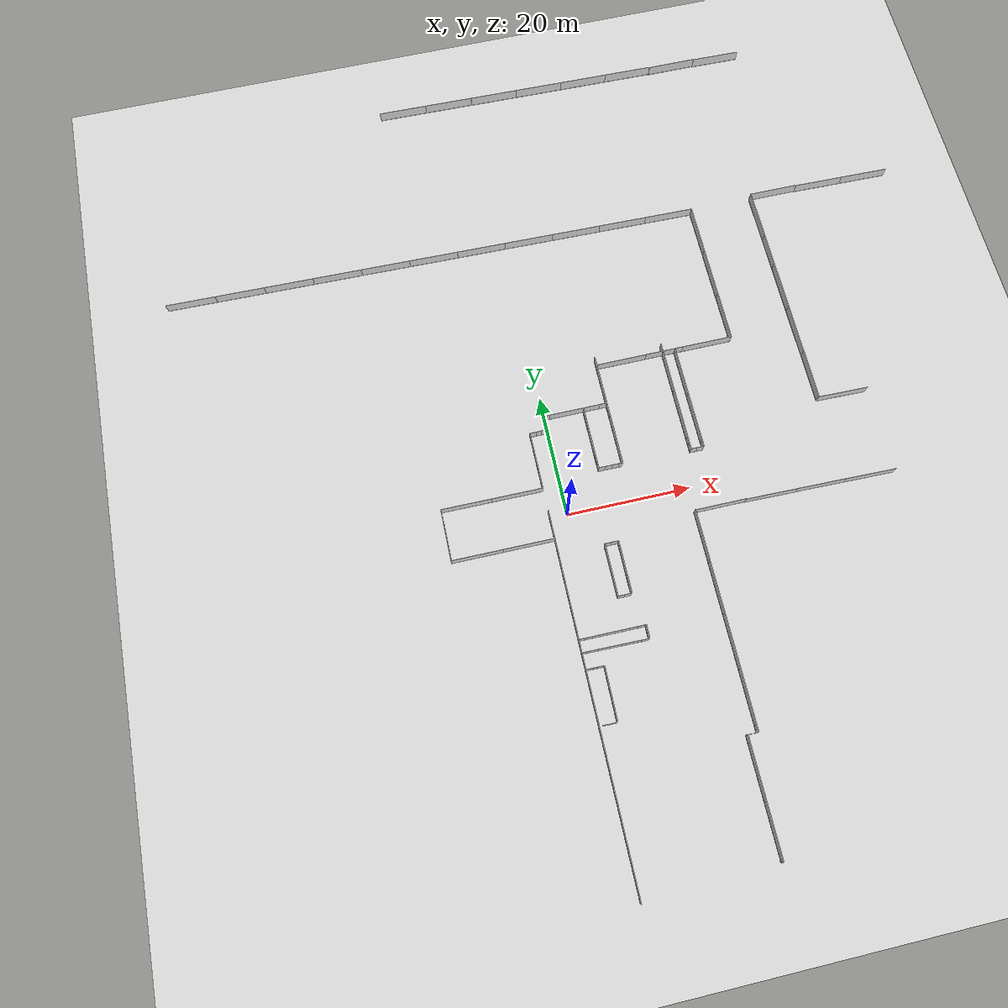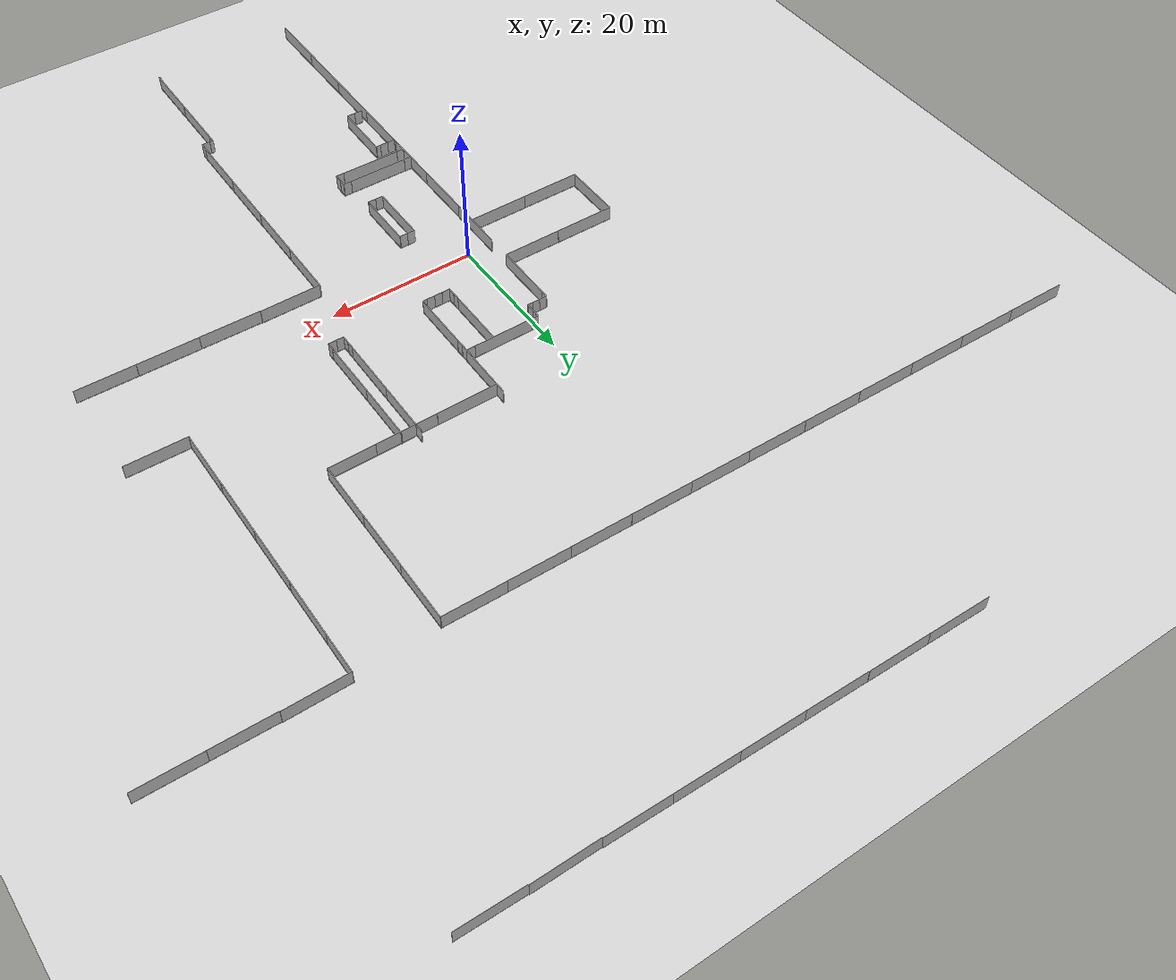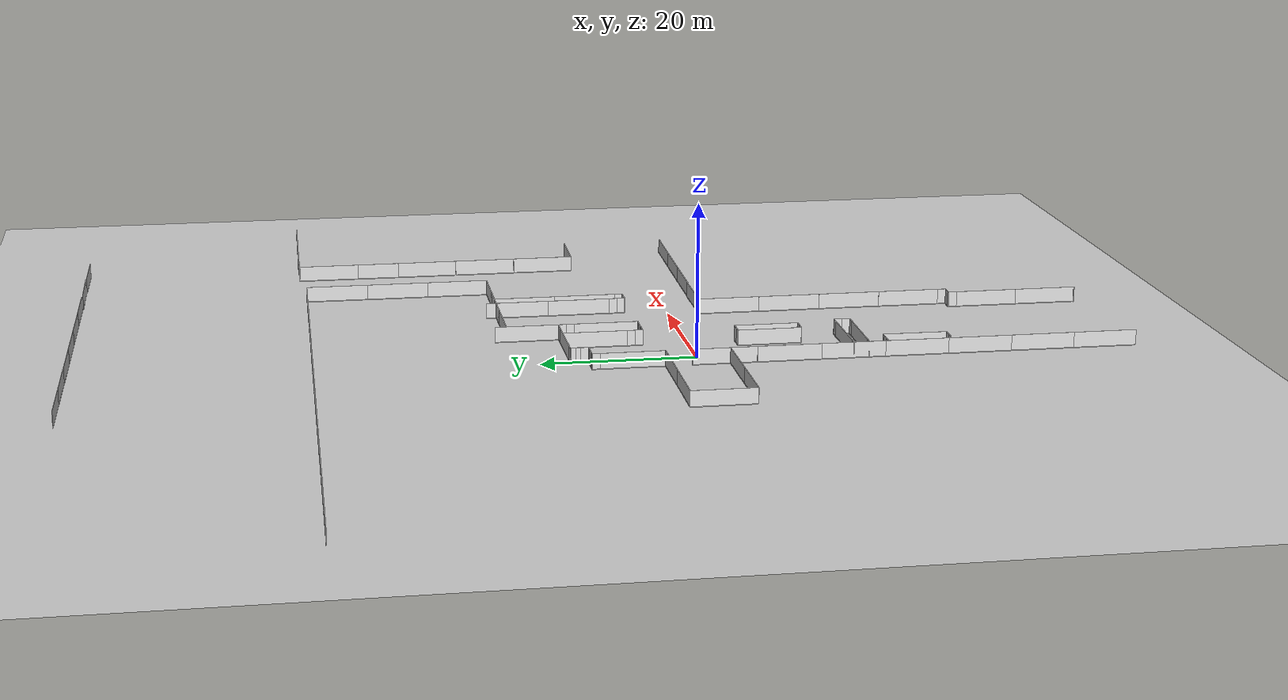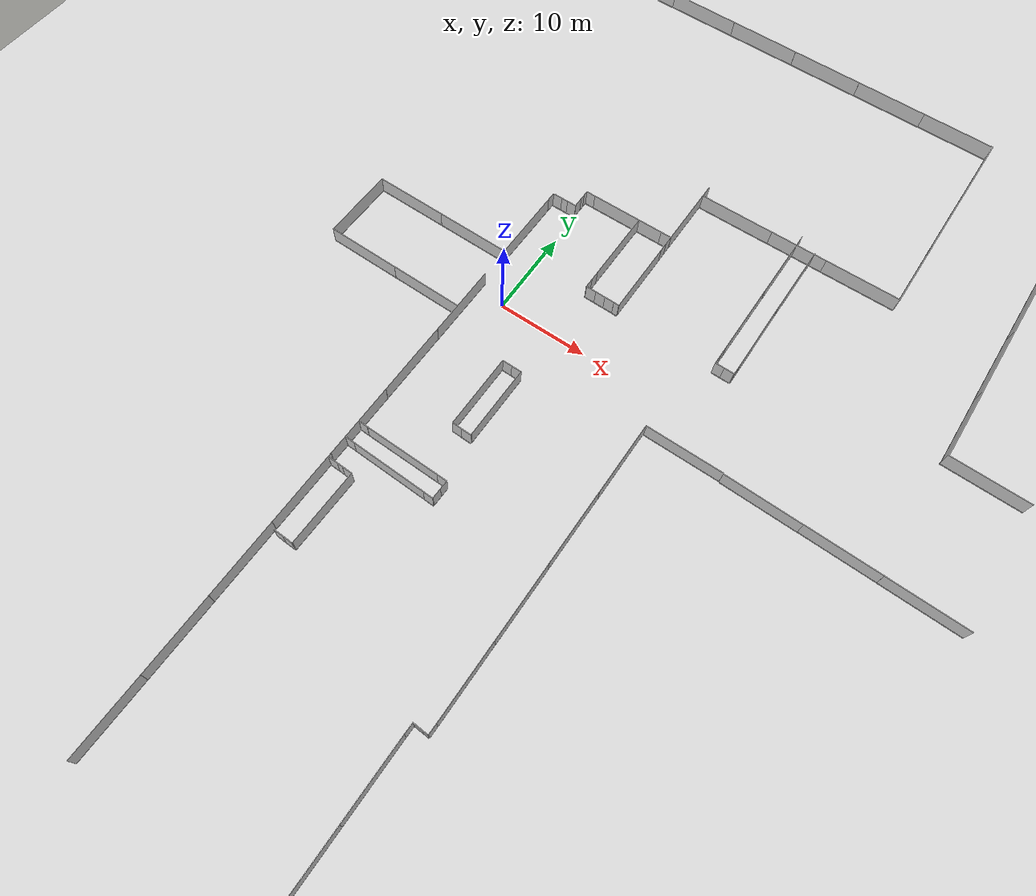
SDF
<sdf version="1.6">
 <world name="default">
  <light name="sun" type="directional">
   <pose>0 0 10 0 -0 0</pose>
   <diffuse>0.8 0.8 0.8 1</diffuse>
   <specular>0.2 0.2 0.2 1</specular>
   <attenuation>
    <range>1000</range>
    <constant>0.9</constant>
    <linear>0.01</linear>
    <quadratic>0.001</quadratic>
   </attenuation>
   <direction>-0.5 0.1 -0.9</direction>
  </light>
  <model name="ground_plane">
   <static>1</static>
   <link name="link">
    <collision name="collision">
     <geometry><plane><normal>0 0 1</normal><size>100 100</size></plane></geometry>
     <surface><friction><ode><mu>100</mu><mu2>50</mu2></ode></friction></surface>
    </collision>
    <visual name="visual">
     <cast_shadows>0</cast_shadows>
     <geometry><plane><normal>0 0 1</normal><size>100 100</size></plane></geometry>
     <material>
      <script><uri>file://media/materials/scripts/gazebo.material</uri><name>Gazebo/Grey</name></script>
     </material>
    </visual>
    <velocity_decay><linear>0</linear><angular>0</angular></velocity_decay>
   </link>
  </model>
  <physics name="default_physics" default="0" type="ode">
   <max_step_size>0.001</max_step_size>
   <real_time_factor>1</real_time_factor>
   <real_time_update_rate>1000</real_time_update_rate>
  </physics>
  <scene><ambient>0.4 0.4 0.4 1</ambient><background>0.7 0.7 0.7 1</background><shadows>1</shadows></scene>
  <spherical_coordinates>
   <surface_model>EARTH_WGS84</surface_model>
   <latitude_deg>0</latitude_deg>
   <longitude_deg>0</longitude_deg>
   <elevation>0</elevation>
   <heading_deg>0</heading_deg>
  </spherical_coordinates>
  <gravity>0 0 -9.8</gravity>
  <magnetic_field>6e-06 2.3e-05 -4.2e-05</magnetic_field>
  <atmosphere type="adiabatic"/>
  <model name="full_wall_55_8295_2090">
   <link name="link">
    <inertial>
     <mass>50</mass>
     <inertia><ixx>1</ixx><ixy>0</ixy><ixz>0</ixz><iyy>1</iyy><iyz>0</iyz><izz>1</izz></inertia>
    </inertial>
    <visual name="bottom_frame">
     <pose>0 0 0.05 0 -0 0</pose>
     <geometry><box><size>0.055 8.295 0.1</size></box></geometry>
     <material>
      <script><uri>model://base_materials/color/scripts</uri><name>hsr_color/white</name></script>
     </material>
    </visual>
    <collision name="collision_bottom_frame">
     <pose>0 0 0.05 0 -0 0</pose>
     <geometry><box><size>0.055 8.295 0.1</size></box></geometry>
    </collision>
    <visual name="wall">
     <pose>0 0 1.095 0 -0 0</pose>
     <geometry><box><size>0.055 8.295 1.99</size></box></geometry>
     <material>
      <script>
       <uri>model://base_materials/wall/scripts</uri>
       <uri>model://base_materials/wall/textures</uri>
       <name>wall/white_noise</name>
      </script>
     </material>
    </visual>
    <collision name="collision_wall">
     <pose>0 0 1.095 0 -0 0</pose>
     <geometry><box><size>0.055 8.295 1.99</size></box></geometry>
    </collision>
    <velocity_decay><linear>0</linear><angular>0</angular></velocity_decay>
   </link>
   <static>1</static>
   <pose>-2.99017 -2.98151 0 0 -0 0</pose>
  </model>
  <model name="full_wall_55_8295_2090_clone">
   <link name="link">
    <inertial>
     <mass>50</mass>
     <inertia><ixx>1</ixx><ixy>0</ixy><ixz>0</ixz><iyy>1</iyy><iyz>0</iyz><izz>1</izz></inertia>
    </inertial>
    <visual name="bottom_frame">
     <pose>0 0 0.05 0 -0 0</pose>
     <geometry><box><size>0.055 8.295 0.1</size></box></geometry>
     <material>
      <script><uri>model://base_materials/color/scripts</uri><name>hsr_color/white</name></script>
     </material>
    </visual>
    <collision name="collision_bottom_frame">
     <pose>0 0 0.05 0 -0 0</pose>
     <geometry><box><size>0.055 8.295 0.1</size></box></geometry>
    </collision>
    <visual name="wall">
     <pose>0 0 1.095 0 -0 0</pose>
     <geometry><box><size>0.055 8.295 1.99</size></box></geometry>
     <material>
      <script>
       <uri>model://base_materials/wall/scripts</uri>
       <uri>model://base_materials/wall/textures</uri>
       <name>wall/white_noise</name>
      </script>
     </material>
    </visual>
    <collision name="collision_wall">
     <pose>0 0 1.095 0 -0 0</pose>
     <geometry><box><size>0.055 8.295 1.99</size></box></geometry>
    </collision>
    <velocity_decay><linear>0</linear><angular>0</angular></velocity_decay>
   </link>
   <static>1</static>
   <pose>-3.00555 8.72228 0 0 -0 0</pose>
  </model>
  <model name="full_wall_55_8295_2090_clone_0">
   <link name="link">
    <inertial>
     <mass>50</mass>
     <inertia><ixx>1</ixx><ixy>0</ixy><ixz>0</ixz><iyy>1</iyy><iyz>0</iyz><izz>1</izz></inertia>
    </inertial>
    <visual name="bottom_frame">
     <pose>0 0 0.05 0 -0 0</pose>
     <geometry><box><size>0.055 8.295 0.1</size></box></geometry>
     <material>
      <script><uri>model://base_materials/color/scripts</uri><name>hsr_color/white</name></script>
     </material>
    </visual>
    <collision name="collision_bottom_frame">
     <pose>0 0 0.05 0 -0 0</pose>
     <geometry><box><size>0.055 8.295 0.1</size></box></geometry>
    </collision>
    <visual name="wall">
     <pose>0 0 1.095 0 -0 0</pose>
     <geometry><box><size>0.055 8.295 1.99</size></box></geometry>
     <material>
      <script>
       <uri>model://base_materials/wall/scripts</uri>
       <uri>model://base_materials/wall/textures</uri>
       <name>wall/white_noise</name>
      </script>
     </material>
    </visual>
    <collision name="collision_wall">
     <pose>0 0 1.095 0 -0 0</pose>
     <geometry><box><size>0.055 8.295 1.99</size></box></geometry>
    </collision>
    <velocity_decay><linear>0</linear><angular>0</angular></velocity_decay>
   </link>
   <static>1</static>
   <pose>-2.99856 -11.2922 0 0 -0 0</pose>
  </model>
  <model name="full_wall_55_8295_2090_clone_clone">
   <link name="link">
    <inertial>
     <mass>50</mass>
     <inertia><ixx>1</ixx><ixy>0</ixy><ixz>0</ixz><iyy>1</iyy><iyz>0</iyz><izz>1</izz></inertia>
    </inertial>
    <visual name="bottom_frame">
     <pose>0 0 0.05 0 -0 0</pose>
     <geometry><box><size>0.055 8.295 0.1</size></box></geometry>
     <material>
      <script><uri>model://base_materials/color/scripts</uri><name>hsr_color/white</name></script>
     </material>
    </visual>
    <collision name="collision_bottom_frame">
     <pose>0 0 0.05 0 -0 0</pose>
     <geometry><box><size>0.055 8.295 0.1</size></box></geometry>
    </collision>
    <visual name="wall">
     <pose>0 0 1.095 0 -0 0</pose>
     <geometry><box><size>0.055 8.295 1.99</size></box></geometry>
     <material>
      <script>
       <uri>model://base_materials/wall/scripts</uri>
       <uri>model://base_materials/wall/textures</uri>
       <name>wall/white_noise</name>
      </script>
     </material>
    </visual>
    <collision name="collision_wall">
     <pose>0 0 1.095 0 -0 0</pose>
     <geometry><box><size>0.055 8.295 1.99</size></box></geometry>
    </collision>
    <velocity_decay><linear>0</linear><angular>0</angular></velocity_decay>
   </link>
   <static>1</static>
   <pose>4.38146 -10.3897 0 0 -0 0</pose>
  </model>
  <model name="full_wall_55_900_2090">
   <link name="link">
    <inertial>
     <mass>50</mass>
     <inertia><ixx>1</ixx><ixy>0</ixy><ixz>0</ixz><iyy>1</iyy><iyz>0</iyz><izz>1</izz></inertia>
    </inertial>
    <visual name="bottom_frame">
     <pose>0 0 0.05 0 -0 0</pose>
     <geometry><box><size>0.055 1.04 0.1</size></box></geometry>
     <material>
      <script><uri>model://base_materials/color/scripts</uri><name>hsr_color/white</name></script>
     </material>
    </visual>
    <collision name="collision_bottom_frame">
     <pose>0 0 0.05 0 -0 0</pose>
     <geometry><box><size>0.055 1.04 0.1</size></box></geometry>
    </collision>
    <visual name="wall">
     <pose>0 0 1.095 0 -0 0</pose>
     <geometry><box><size>0.055 1.04 1.99</size></box></geometry>
     <material>
      <script>
       <uri>model://base_materials/wall/scripts</uri>
       <uri>model://base_materials/wall/textures</uri>
       <name>wall/white_noise</name>
      </script>
     </material>
    </visual>
    <collision name="collision_wall">
     <pose>0 0 1.095 0 -0 0</pose>
     <geometry><box><size>0.055 1.04 1.99</size></box></geometry>
    </collision>
    <velocity_decay><linear>0</linear><angular>0</angular></velocity_decay>
   </link>
   <static>1</static>
   <pose>-3.01014 13.3927 0 0 -0 0</pose>
  </model>
  <model name="full_wall_55_900_2090_clone">
   <link name="link">
    <inertial>
     <mass>50</mass>
     <inertia><ixx>1</ixx><ixy>0</ixy><ixz>0</ixz><iyy>1</iyy><iyz>0</iyz><izz>1</izz></inertia>
    </inertial>
    <visual name="bottom_frame">
     <pose>0 0 0.05 0 -0 0</pose>
     <geometry><box><size>0.055 1.04 0.1</size></box></geometry>
     <material>
      <script><uri>model://base_materials/color/scripts</uri><name>hsr_color/white</name></script>
     </material>
    </visual>
    <collision name="collision_bottom_frame">
     <pose>0 0 0.05 0 -0 0</pose>
     <geometry><box><size>0.055 1.04 0.1</size></box></geometry>
    </collision>
    <visual name="wall">
     <pose>0 0 1.095 0 -0 0</pose>
     <geometry><box><size>0.055 1.04 1.99</size></box></geometry>
     <material>
      <script>
       <uri>model://base_materials/wall/scripts</uri>
       <uri>model://base_materials/wall/textures</uri>
       <name>wall/white_noise</name>
      </script>
     </material>
    </visual>
    <collision name="collision_wall">
     <pose>0 0 1.095 0 -0 0</pose>
     <geometry><box><size>0.055 1.04 1.99</size></box></geometry>
    </collision>
    <velocity_decay><linear>0</linear><angular>0</angular></velocity_decay>
   </link>
   <static>1</static>
   <pose>-2.45128 13.9047 -0.00246 0 0 -1.56434</pose>
  </model>
  <model name="full_wall_55_900_2090_clone_clone">
   <link name="link">
    <inertial>
     <mass>50</mass>
     <inertia><ixx>1</ixx><ixy>0</ixy><ixz>0</ixz><iyy>1</iyy><iyz>0</iyz><izz>1</izz></inertia>
    </inertial>
    <visual name="bottom_frame">
     <pose>0 0 0.05 0 -0 0</pose>
     <geometry><box><size>0.055 1.04 0.1</size></box></geometry>
     <material>
      <script><uri>model://base_materials/color/scripts</uri><name>hsr_color/white</name></script>
     </material>
    </visual>
    <collision name="collision_bottom_frame">
     <pose>0 0 0.05 0 -0 0</pose>
     <geometry><box><size>0.055 1.04 0.1</size></box></geometry>
    </collision>
    <visual name="wall">
     <pose>0 0 1.095 0 -0 0</pose>
     <geometry><box><size>0.055 1.04 1.99</size></box></geometry>
     <material>
      <script>
       <uri>model://base_materials/wall/scripts</uri>
       <uri>model://base_materials/wall/textures</uri>
       <name>wall/white_noise</name>
      </script>
     </material>
    </visual>
    <collision name="collision_wall">
     <pose>0 0 1.095 0 -0 0</pose>
     <geometry><box><size>0.055 1.04 1.99</size></box></geometry>
    </collision>
    <velocity_decay><linear>0</linear><angular>0</angular></velocity_decay>
   </link>
   <static>1</static>
   <pose>-1.41364 13.9135 -0.010067 0 0 -1.56434</pose>
  </model>
  <model name="full_wall_55_8295_2090_clone_0_clone_0">
   <link name="link">
    <inertial>
     <mass>50</mass>
     <inertia><ixx>1</ixx><ixy>0</ixy><ixz>0</ixz><iyy>1</iyy><iyz>0</iyz><izz>1</izz></inertia>
    </inertial>
    <visual name="bottom_frame">
     <pose>0 0 0.05 0 -0 0</pose>
     <geometry><box><size>0.055 8.295 0.1</size></box></geometry>
     <material>
      <script><uri>model://base_materials/color/scripts</uri><name>hsr_color/white</name></script>
     </material>
    </visual>
    <collision name="collision_bottom_frame">
     <pose>0 0 0.05 0 -0 0</pose>
     <geometry><box><size>0.055 8.295 0.1</size></box></geometry>
    </collision>
    <visual name="wall">
     <pose>0 0 1.095 0 -0 0</pose>
     <geometry><box><size>0.055 8.295 1.99</size></box></geometry>
     <material>
      <script>
       <uri>model://base_materials/wall/scripts</uri>
       <uri>model://base_materials/wall/textures</uri>
       <name>wall/white_noise</name>
      </script>
     </material>
    </visual>
    <collision name="collision_wall">
     <pose>0 0 1.095 0 -0 0</pose>
     <geometry><box><size>0.055 8.295 1.99</size></box></geometry>
    </collision>
    <velocity_decay><linear>0</linear><angular>0</angular></velocity_decay>
   </link>
   <static>1</static>
   <pose>-2.99358 -19.6031 0 0 -0 0</pose>
  </model>
  <model name="full_wall_55_900_2090_clone_0">
   <link name="link">
    <inertial>
     <mass>50</mass>
     <inertia><ixx>1</ixx><ixy>0</ixy><ixz>0</ixz><iyy>1</iyy><iyz>0</iyz><izz>1</izz></inertia>
    </inertial>
    <visual name="bottom_frame">
     <pose>0 0 0.05 0 -0 0</pose>
     <geometry><box><size>0.055 1.04 0.1</size></box></geometry>
     <material>
      <script><uri>model://base_materials/color/scripts</uri><name>hsr_color/white</name></script>
     </material>
    </visual>
    <collision name="collision_bottom_frame">
     <pose>0 0 0.05 0 -0 0</pose>
     <geometry><box><size>0.055 1.04 0.1</size></box></geometry>
    </collision>
    <visual name="wall">
     <pose>0 0 1.095 0 -0 0</pose>
     <geometry><box><size>0.055 1.04 1.99</size></box></geometry>
     <material>
      <script>
       <uri>model://base_materials/wall/scripts</uri>
       <uri>model://base_materials/wall/textures</uri>
       <name>wall/white_noise</name>
      </script>
     </material>
    </visual>
    <collision name="collision_wall">
     <pose>0 0 1.095 0 -0 0</pose>
     <geometry><box><size>0.055 1.04 1.99</size></box></geometry>
    </collision>
    <velocity_decay><linear>0</linear><angular>0</angular></velocity_decay>
   </link>
   <static>1</static>
   <pose>-0.19817 14.4732 0 0 -0 0</pose>
  </model>
  <model name="full_wall_55_600_2090">
   <link name="link">
    <inertial>
     <mass>50</mass>
     <inertia><ixx>1</ixx><ixy>0</ixy><ixz>0</ixz><iyy>1</iyy><iyz>0</iyz><izz>1</izz></inertia>
    </inertial>
    <visual name="bottom_frame">
     <pose>0 0 0.05 0 -0 0</pose>
     <geometry><box><size>0.055 0.6 0.1</size></box></geometry>
     <material>
      <script><uri>model://base_materials/color/scripts</uri><name>hsr_color/white</name></script>
     </material>
    </visual>
    <collision name="collision_bottom_frame">
     <pose>0 0 0.05 0 -0 0</pose>
     <geometry><box><size>0.055 0.6 0.1</size></box></geometry>
    </collision>
    <visual name="wall">
     <pose>0 0 1.095 0 -0 0</pose>
     <geometry><box><size>0.055 0.6 1.99</size></box></geometry>
     <material>
      <script>
       <uri>model://base_materials/wall/scripts</uri>
       <uri>model://base_materials/wall/textures</uri>
       <name>wall/white_noise</name>
      </script>
     </material>
    </visual>
    <collision name="collision_wall">
     <pose>0 0 1.095 0 -0 0</pose>
     <geometry><box><size>0.055 0.6 1.99</size></box></geometry>
    </collision>
    <velocity_decay><linear>0</linear><angular>0</angular></velocity_decay>
   </link>
   <static>1</static>
   <pose>-0.19825 15.2907 0 0 -0 0</pose>
  </model>
  <model name="full_wall_55_900_2090_clone_clone_clone">
   <link name="link">
    <inertial>
     <mass>50</mass>
     <inertia><ixx>1</ixx><ixy>0</ixy><ixz>0</ixz><iyy>1</iyy><iyz>0</iyz><izz>1</izz></inertia>
    </inertial>
    <visual name="bottom_frame">
     <pose>0 0 0.05 0 -0 0</pose>
     <geometry><box><size>0.055 1.04 0.1</size></box></geometry>
     <material>
      <script><uri>model://base_materials/color/scripts</uri><name>hsr_color/white</name></script>
     </material>
    </visual>
    <collision name="collision_bottom_frame">
     <pose>0 0 0.05 0 -0 0</pose>
     <geometry><box><size>0.055 1.04 0.1</size></box></geometry>
    </collision>
    <visual name="wall">
     <pose>0 0 1.095 0 -0 0</pose>
     <geometry><box><size>0.055 1.04 1.99</size></box></geometry>
     <material>
      <script>
       <uri>model://base_materials/wall/scripts</uri>
       <uri>model://base_materials/wall/textures</uri>
       <name>wall/white_noise</name>
      </script>
     </material>
    </visual>
    <collision name="collision_wall">
     <pose>0 0 1.095 0 -0 0</pose>
     <geometry><box><size>0.055 1.04 1.99</size></box></geometry>
    </collision>
    <velocity_decay><linear>0</linear><angular>0</angular></velocity_decay>
   </link>
   <static>1</static>
   <pose>0.300147 16.2353 -0.010067 0 0 -1.56434</pose>
  </model>
  <model name="full_wall_55_8295_2090_clone_clone_0">
   <link name="link">
    <inertial>
     <mass>50</mass>
     <inertia><ixx>1</ixx><ixy>0</ixy><ixz>0</ixz><iyy>1</iyy><iyz>0</iyz><izz>1</izz></inertia>
    </inertial>
    <visual name="bottom_frame">
     <pose>0 0 0.05 0 -0 0</pose>
     <geometry><box><size>0.055 8.295 0.1</size></box></geometry>
     <material>
      <script><uri>model://base_materials/color/scripts</uri><name>hsr_color/white</name></script>
     </material>
    </visual>
    <collision name="collision_bottom_frame">
     <pose>0 0 0.05 0 -0 0</pose>
     <geometry><box><size>0.055 8.295 0.1</size></box></geometry>
    </collision>
    <visual name="wall">
     <pose>0 0 1.095 0 -0 0</pose>
     <geometry><box><size>0.055 8.295 1.99</size></box></geometry>
     <material>
      <script>
       <uri>model://base_materials/wall/scripts</uri>
       <uri>model://base_materials/wall/textures</uri>
       <name>wall/white_noise</name>
      </script>
     </material>
    </visual>
    <collision name="collision_wall">
     <pose>0 0 1.095 0 -0 0</pose>
     <geometry><box><size>0.055 8.295 1.99</size></box></geometry>
    </collision>
    <velocity_decay><linear>0</linear><angular>0</angular></velocity_decay>
   </link>
   <static>1</static>
   <pose>4.96886 16.2397 0 0 -0 1.5723</pose>
  </model>
  <model name="full_wall_55_600_2090_clone">
   <link name="link">
    <inertial>
     <mass>50</mass>
     <inertia><ixx>1</ixx><ixy>0</ixy><ixz>0</ixz><iyy>1</iyy><iyz>0</iyz><izz>1</izz></inertia>
    </inertial>
    <visual name="bottom_frame">
     <pose>0 0 0.05 0 -0 0</pose>
     <geometry><box><size>0.055 0.6 0.1</size></box></geometry>
     <material>
      <script><uri>model://base_materials/color/scripts</uri><name>hsr_color/white</name></script>
     </material>
    </visual>
    <collision name="collision_bottom_frame">
     <pose>0 0 0.05 0 -0 0</pose>
     <geometry><box><size>0.055 0.6 0.1</size></box></geometry>
    </collision>
    <visual name="wall">
     <pose>0 0 1.095 0 -0 0</pose>
     <geometry><box><size>0.055 0.6 1.99</size></box></geometry>
     <material>
      <script>
       <uri>model://base_materials/wall/scripts</uri>
       <uri>model://base_materials/wall/textures</uri>
       <name>wall/white_noise</name>
      </script>
     </material>
    </visual>
    <collision name="collision_wall">
     <pose>0 0 1.095 0 -0 0</pose>
     <geometry><box><size>0.055 0.6 1.99</size></box></geometry>
    </collision>
    <velocity_decay><linear>0</linear><angular>0</angular></velocity_decay>
   </link>
   <static>1</static>
   <pose>-0.202043 15.8892 0 0 -0 0</pose>
  </model>
  <model name="full_wall_55_900_2090_clone_clone_clone_clone">
   <link name="link">
    <inertial>
     <mass>50</mass>
     <inertia><ixx>1</ixx><ixy>0</ixy><ixz>0</ixz><iyy>1</iyy><iyz>0</iyz><izz>1</izz></inertia>
    </inertial>
    <visual name="bottom_frame">
     <pose>0 0 0.05 0 -0 0</pose>
     <geometry><box><size>0.055 1.04 0.1</size></box></geometry>
     <material>
      <script><uri>model://base_materials/color/scripts</uri><name>hsr_color/white</name></script>
     </material>
    </visual>
    <collision name="collision_bottom_frame">
     <pose>0 0 0.05 0 -0 0</pose>
     <geometry><box><size>0.055 1.04 0.1</size></box></geometry>
    </collision>
    <visual name="wall">
     <pose>0 0 1.095 0 -0 0</pose>
     <geometry><box><size>0.055 1.04 1.99</size></box></geometry>
     <material>
      <script>
       <uri>model://base_materials/wall/scripts</uri>
       <uri>model://base_materials/wall/textures</uri>
       <name>wall/white_noise</name>
      </script>
     </material>
    </visual>
    <collision name="collision_wall">
     <pose>0 0 1.095 0 -0 0</pose>
     <geometry><box><size>0.055 1.04 1.99</size></box></geometry>
    </collision>
    <velocity_decay><linear>0</linear><angular>0</angular></velocity_decay>
   </link>
   <static>1</static>
   <pose>-0.688198 13.9166 -0.010067 0 0 -1.56434</pose>
  </model>
  <model name="full_wall_55_8295_2090_0">
   <link name="link">
    <inertial>
     <mass>50</mass>
     <inertia><ixx>1</ixx><ixy>0</ixy><ixz>0</ixz><iyy>1</iyy><iyz>0</iyz><izz>1</izz></inertia>
    </inertial>
    <visual name="bottom_frame">
     <pose>0 0 0.05 0 -0 0</pose>
     <geometry><box><size>0.055 8.295 0.1</size></box></geometry>
     <material>
      <script><uri>model://base_materials/color/scripts</uri><name>hsr_color/white</name></script>
     </material>
    </visual>
    <collision name="collision_bottom_frame">
     <pose>0 0 0.05 0 -0 0</pose>
     <geometry><box><size>0.055 8.295 0.1</size></box></geometry>
    </collision>
    <visual name="wall">
     <pose>0 0 1.095 0 -0 0</pose>
     <geometry><box><size>0.055 8.295 1.99</size></box></geometry>
     <material>
      <script>
       <uri>model://base_materials/wall/scripts</uri>
       <uri>model://base_materials/wall/textures</uri>
       <name>wall/white_noise</name>
      </script>
     </material>
    </visual>
    <collision name="collision_wall">
     <pose>0 0 1.095 0 -0 0</pose>
     <geometry><box><size>0.055 8.295 1.99</size></box></geometry>
    </collision>
    <velocity_decay><linear>0</linear><angular>0</angular></velocity_decay>
   </link>
   <static>1</static>
   <pose>6.38003 12.0767 0 0 -0 0</pose>
  </model>
  <model name="full_wall_55_900_2090_clone_0_clone">
   <link name="link">
    <inertial>
     <mass>50</mass>
     <inertia><ixx>1</ixx><ixy>0</ixy><ixz>0</ixz><iyy>1</iyy><iyz>0</iyz><izz>1</izz></inertia>
    </inertial>
    <visual name="bottom_frame">
     <pose>0 0 0.05 0 -0 0</pose>
     <geometry><box><size>0.055 1.04 0.1</size></box></geometry>
     <material>
      <script><uri>model://base_materials/color/scripts</uri><name>hsr_color/white</name></script>
     </material>
    </visual>
    <collision name="collision_bottom_frame">
     <pose>0 0 0.05 0 -0 0</pose>
     <geometry><box><size>0.055 1.04 0.1</size></box></geometry>
    </collision>
    <visual name="wall">
     <pose>0 0 1.095 0 -0 0</pose>
     <geometry><box><size>0.055 1.04 1.99</size></box></geometry>
     <material>
      <script>
       <uri>model://base_materials/wall/scripts</uri>
       <uri>model://base_materials/wall/textures</uri>
       <name>wall/white_noise</name>
      </script>
     </material>
    </visual>
    <collision name="collision_wall">
     <pose>0 0 1.095 0 -0 0</pose>
     <geometry><box><size>0.055 1.04 1.99</size></box></geometry>
    </collision>
    <velocity_decay><linear>0</linear><angular>0</angular></velocity_decay>
   </link>
   <static>1</static>
   <pose>6.38058 7.40801 0 0 -0 0</pose>
  </model>
  <model name="full_wall_55_900_2090_clone_0_clone_clone">
   <link name="link">
    <inertial>
     <mass>50</mass>
     <inertia><ixx>1</ixx><ixy>0</ixy><ixz>0</ixz><iyy>1</iyy><iyz>0</iyz><izz>1</izz></inertia>
    </inertial>
    <visual name="bottom_frame">
     <pose>0 0 0.05 0 -0 0</pose>
     <geometry><box><size>0.055 1.04 0.1</size></box></geometry>
     <material>
      <script><uri>model://base_materials/color/scripts</uri><name>hsr_color/white</name></script>
     </material>
    </visual>
    <collision name="collision_bottom_frame">
     <pose>0 0 0.05 0 -0 0</pose>
     <geometry><box><size>0.055 1.04 0.1</size></box></geometry>
    </collision>
    <visual name="wall">
     <pose>0 0 1.095 0 -0 0</pose>
     <geometry><box><size>0.055 1.04 1.99</size></box></geometry>
     <material>
      <script>
       <uri>model://base_materials/wall/scripts</uri>
       <uri>model://base_materials/wall/textures</uri>
       <name>wall/white_noise</name>
      </script>
     </material>
    </visual>
    <collision name="collision_wall">
     <pose>0 0 1.095 0 -0 0</pose>
     <geometry><box><size>0.055 1.04 1.99</size></box></geometry>
    </collision>
    <velocity_decay><linear>0</linear><angular>0</angular></velocity_decay>
   </link>
   <static>1</static>
   <pose>6.38364 6.36759 0 0 -0 0</pose>
  </model>
  <model name="full_wall_55_1100_2090">
   <link name="link">
    <inertial>
     <mass>50</mass>
     <inertia><ixx>1</ixx><ixy>0</ixy><ixz>0</ixz><iyy>1</iyy><iyz>0</iyz><izz>1</izz></inertia>
    </inertial>
    <visual name="bottom_frame">
     <pose>0 0 0.05 0 -0 0</pose>
     <geometry><box><size>0.055 1.1 0.1</size></box></geometry>
     <material>
      <script><uri>model://base_materials/color/scripts</uri><name>hsr_color/white</name></script>
     </material>
    </visual>
    <collision name="collision_bottom_frame">
     <pose>0 0 0.05 0 -0 0</pose>
     <geometry><box><size>0.055 1.1 0.1</size></box></geometry>
    </collision>
    <visual name="wall">
     <pose>0 0 1.095 0 -0 0</pose>
     <geometry><box><size>0.055 1.1 1.99</size></box></geometry>
     <material>
      <script>
       <uri>model://base_materials/wall/scripts</uri>
       <uri>model://base_materials/wall/textures</uri>
       <name>wall/white_noise</name>
      </script>
     </material>
    </visual>
    <collision name="collision_wall">
     <pose>0 0 1.095 0 -0 0</pose>
     <geometry><box><size>0.055 1.1 1.99</size></box></geometry>
    </collision>
    <velocity_decay><linear>0</linear><angular>0</angular></velocity_decay>
   </link>
   <static>1</static>
   <pose>6.96732 5.88036 0 0 -0 1.56492</pose>
  </model>
  <model name="full_wall_55_1100_2090_clone">
   <link name="link">
    <inertial>
     <mass>50</mass>
     <inertia><ixx>1</ixx><ixy>0</ixy><ixz>0</ixz><iyy>1</iyy><iyz>0</iyz><izz>1</izz></inertia>
    </inertial>
    <visual name="bottom_frame">
     <pose>0 0 0.05 0 -0 0</pose>
     <geometry><box><size>0.055 1.1 0.1</size></box></geometry>
     <material>
      <script><uri>model://base_materials/color/scripts</uri><name>hsr_color/white</name></script>
     </material>
    </visual>
    <collision name="collision_bottom_frame">
     <pose>0 0 0.05 0 -0 0</pose>
     <geometry><box><size>0.055 1.1 0.1</size></box></geometry>
    </collision>
    <visual name="wall">
     <pose>0 0 1.095 0 -0 0</pose>
     <geometry><box><size>0.055 1.1 1.99</size></box></geometry>
     <material>
      <script>
       <uri>model://base_materials/wall/scripts</uri>
       <uri>model://base_materials/wall/textures</uri>
       <name>wall/white_noise</name>
      </script>
     </material>
    </visual>
    <collision name="collision_wall">
     <pose>0 0 1.095 0 -0 0</pose>
     <geometry><box><size>0.055 1.1 1.99</size></box></geometry>
    </collision>
    <velocity_decay><linear>0</linear><angular>0</angular></velocity_decay>
   </link>
   <static>1</static>
   <pose>8.07351 5.87309 0 0 -0 1.56492</pose>
  </model>
  <model name="full_wall_55_1100_2090_clone_clone">
   <link name="link">
    <inertial>
     <mass>50</mass>
     <inertia><ixx>1</ixx><ixy>0</ixy><ixz>0</ixz><iyy>1</iyy><iyz>0</iyz><izz>1</izz></inertia>
    </inertial>
    <visual name="bottom_frame">
     <pose>0 0 0.05 0 -0 0</pose>
     <geometry><box><size>0.055 1.1 0.1</size></box></geometry>
     <material>
      <script><uri>model://base_materials/color/scripts</uri><name>hsr_color/white</name></script>
     </material>
    </visual>
    <collision name="collision_bottom_frame">
     <pose>0 0 0.05 0 -0 0</pose>
     <geometry><box><size>0.055 1.1 0.1</size></box></geometry>
    </collision>
    <visual name="wall">
     <pose>0 0 1.095 0 -0 0</pose>
     <geometry><box><size>0.055 1.1 1.99</size></box></geometry>
     <material>
      <script>
       <uri>model://base_materials/wall/scripts</uri>
       <uri>model://base_materials/wall/textures</uri>
       <name>wall/white_noise</name>
      </script>
     </material>
    </visual>
    <collision name="collision_wall">
     <pose>0 0 1.095 0 -0 0</pose>
     <geometry><box><size>0.055 1.1 1.99</size></box></geometry>
    </collision>
    <velocity_decay><linear>0</linear><angular>0</angular></velocity_decay>
   </link>
   <static>1</static>
   <pose>9.15161 5.86887 0 0 -0 1.56492</pose>
  </model>
  <model name="full_wall_55_600_2090_0">
   <link name="link">
    <inertial>
     <mass>50</mass>
     <inertia><ixx>1</ixx><ixy>0</ixy><ixz>0</ixz><iyy>1</iyy><iyz>0</iyz><izz>1</izz></inertia>
    </inertial>
    <visual name="bottom_frame">
     <pose>0 0 0.05 0 -0 0</pose>
     <geometry><box><size>0.055 0.6 0.1</size></box></geometry>
     <material>
      <script><uri>model://base_materials/color/scripts</uri><name>hsr_color/white</name></script>
     </material>
    </visual>
    <collision name="collision_bottom_frame">
     <pose>0 0 0.05 0 -0 0</pose>
     <geometry><box><size>0.055 0.6 0.1</size></box></geometry>
    </collision>
    <visual name="wall">
     <pose>0 0 1.095 0 -0 0</pose>
     <geometry><box><size>0.055 0.6 1.99</size></box></geometry>
     <material>
      <script>
       <uri>model://base_materials/wall/scripts</uri>
       <uri>model://base_materials/wall/textures</uri>
       <name>wall/white_noise</name>
      </script>
     </material>
    </visual>
    <collision name="collision_wall">
     <pose>0 0 1.095 0 -0 0</pose>
     <geometry><box><size>0.055 0.6 1.99</size></box></geometry>
    </collision>
    <velocity_decay><linear>0</linear><angular>0</angular></velocity_decay>
   </link>
   <static>1</static>
   <pose>10.0087 5.85043 0 0 0 -1.60946</pose>
  </model>
  <model name="full_wall_55_8295_2090_0_clone">
   <link name="link">
    <inertial>
     <mass>50</mass>
     <inertia><ixx>1</ixx><ixy>0</ixy><ixz>0</ixz><iyy>1</iyy><iyz>0</iyz><izz>1</izz></inertia>
    </inertial>
    <visual name="bottom_frame">
     <pose>0 0 0.05 0 -0 0</pose>
     <geometry><box><size>0.055 8.295 0.1</size></box></geometry>
     <material>
      <script><uri>model://base_materials/color/scripts</uri><name>hsr_color/white</name></script>
     </material>
    </visual>
    <collision name="collision_bottom_frame">
     <pose>0 0 0.05 0 -0 0</pose>
     <geometry><box><size>0.055 8.295 0.1</size></box></geometry>
    </collision>
    <visual name="wall">
     <pose>0 0 1.095 0 -0 0</pose>
     <geometry><box><size>0.055 8.295 1.99</size></box></geometry>
     <material>
      <script>
       <uri>model://base_materials/wall/scripts</uri>
       <uri>model://base_materials/wall/textures</uri>
       <name>wall/white_noise</name>
      </script>
     </material>
    </visual>
    <collision name="collision_wall">
     <pose>0 0 1.095 0 -0 0</pose>
     <geometry><box><size>0.055 8.295 1.99</size></box></geometry>
    </collision>
    <velocity_decay><linear>0</linear><angular>0</angular></velocity_decay>
   </link>
   <static>1</static>
   <pose>10.3086 10.0337 0 0 -0 0</pose>
  </model>
  <model name="full_wall_55_900_2090_clone_0_clone_clone_0">
   <link name="link">
    <inertial>
     <mass>50</mass>
     <inertia><ixx>1</ixx><ixy>0</ixy><ixz>0</ixz><iyy>1</iyy><iyz>0</iyz><izz>1</izz></inertia>
    </inertial>
    <visual name="bottom_frame">
     <pose>0 0 0.05 0 -0 0</pose>
     <geometry><box><size>0.055 1.04 0.1</size></box></geometry>
     <material>
      <script><uri>model://base_materials/color/scripts</uri><name>hsr_color/white</name></script>
     </material>
    </visual>
    <collision name="collision_bottom_frame">
     <pose>0 0 0.05 0 -0 0</pose>
     <geometry><box><size>0.055 1.04 0.1</size></box></geometry>
    </collision>
    <visual name="wall">
     <pose>0 0 1.095 0 -0 0</pose>
     <geometry><box><size>0.055 1.04 1.99</size></box></geometry>
     <material>
      <script>
       <uri>model://base_materials/wall/scripts</uri>
       <uri>model://base_materials/wall/textures</uri>
       <name>wall/white_noise</name>
      </script>
     </material>
    </visual>
    <collision name="collision_wall">
     <pose>0 0 1.095 0 -0 0</pose>
     <geometry><box><size>0.055 1.04 1.99</size></box></geometry>
    </collision>
    <velocity_decay><linear>0</linear><angular>0</angular></velocity_decay>
   </link>
   <static>1</static>
   <pose>10.2964 14.6983 0 0 -0 0</pose>
  </model>
  <model name="full_wall_55_900_2090_clone_0_clone_clone_clone">
   <link name="link">
    <inertial>
     <mass>50</mass>
     <inertia><ixx>1</ixx><ixy>0</ixy><ixz>0</ixz><iyy>1</iyy><iyz>0</iyz><izz>1</izz></inertia>
    </inertial>
    <visual name="bottom_frame">
     <pose>0 0 0.05 0 -0 0</pose>
     <geometry><box><size>0.055 1.04 0.1</size></box></geometry>
     <material>
      <script><uri>model://base_materials/color/scripts</uri><name>hsr_color/white</name></script>
     </material>
    </visual>
    <collision name="collision_bottom_frame">
     <pose>0 0 0.05 0 -0 0</pose>
     <geometry><box><size>0.055 1.04 0.1</size></box></geometry>
    </collision>
    <visual name="wall">
     <pose>0 0 1.095 0 -0 0</pose>
     <geometry><box><size>0.055 1.04 1.99</size></box></geometry>
     <material>
      <script>
       <uri>model://base_materials/wall/scripts</uri>
       <uri>model://base_materials/wall/textures</uri>
       <name>wall/white_noise</name>
      </script>
     </material>
    </visual>
    <collision name="collision_wall">
     <pose>0 0 1.095 0 -0 0</pose>
     <geometry><box><size>0.055 1.04 1.99</size></box></geometry>
    </collision>
    <velocity_decay><linear>0</linear><angular>0</angular></velocity_decay>
   </link>
   <static>1</static>
   <pose>10.2876 15.7375 0 0 -0 0</pose>
  </model>
  <model name="full_wall_55_1100_2090_clone_0">
   <link name="link">
    <inertial>
     <mass>50</mass>
     <inertia><ixx>1</ixx><ixy>0</ixy><ixz>0</ixz><iyy>1</iyy><iyz>0</iyz><izz>1</izz></inertia>
    </inertial>
    <visual name="bottom_frame">
     <pose>0 0 0.05 0 -0 0</pose>
     <geometry><box><size>0.055 1.1 0.1</size></box></geometry>
     <material>
      <script><uri>model://base_materials/color/scripts</uri><name>hsr_color/white</name></script>
     </material>
    </visual>
    <collision name="collision_bottom_frame">
     <pose>0 0 0.05 0 -0 0</pose>
     <geometry><box><size>0.055 1.1 0.1</size></box></geometry>
    </collision>
    <visual name="wall">
     <pose>0 0 1.095 0 -0 0</pose>
     <geometry><box><size>0.055 1.1 1.99</size></box></geometry>
     <material>
      <script>
       <uri>model://base_materials/wall/scripts</uri>
       <uri>model://base_materials/wall/textures</uri>
       <name>wall/white_noise</name>
      </script>
     </material>
    </visual>
    <collision name="collision_wall">
     <pose>0 0 1.095 0 -0 0</pose>
     <geometry><box><size>0.055 1.1 1.99</size></box></geometry>
    </collision>
    <velocity_decay><linear>0</linear><angular>0</angular></velocity_decay>
   </link>
   <static>1</static>
   <pose>9.65739 16.248 0 0 -0 1.56492</pose>
  </model>
  <model name="full_wall_55_8295_2090_clone_clone_1">
   <link name="link">
    <inertial>
     <mass>50</mass>
     <inertia><ixx>1</ixx><ixy>0</ixy><ixz>0</ixz><iyy>1</iyy><iyz>0</iyz><izz>1</izz></inertia>
    </inertial>
    <visual name="bottom_frame">
     <pose>0 0 0.05 0 -0 0</pose>
     <geometry><box><size>0.055 8.295 0.1</size></box></geometry>
     <material>
      <script><uri>model://base_materials/color/scripts</uri><name>hsr_color/white</name></script>
     </material>
    </visual>
    <collision name="collision_bottom_frame">
     <pose>0 0 0.05 0 -0 0</pose>
     <geometry><box><size>0.055 8.295 0.1</size></box></geometry>
    </collision>
    <visual name="wall">
     <pose>0 0 1.095 0 -0 0</pose>
     <geometry><box><size>0.055 8.295 1.99</size></box></geometry>
     <material>
      <script>
       <uri>model://base_materials/wall/scripts</uri>
       <uri>model://base_materials/wall/textures</uri>
       <name>wall/white_noise</name>
      </script>
     </material>
    </visual>
    <collision name="collision_wall">
     <pose>0 0 1.095 0 -0 0</pose>
     <geometry><box><size>0.055 8.295 1.99</size></box></geometry>
    </collision>
    <velocity_decay><linear>0</linear><angular>0</angular></velocity_decay>
   </link>
   <static>1</static>
   <pose>10.3025 20.3737 0 0 -0 0</pose>
  </model>
  <model name="full_wall_55_8295_2090_clone_clone_0_clone">
   <link name="link">
    <inertial>
     <mass>50</mass>
     <inertia><ixx>1</ixx><ixy>0</ixy><ixz>0</ixz><iyy>1</iyy><iyz>0</iyz><izz>1</izz></inertia>
    </inertial>
    <visual name="bottom_frame">
     <pose>0 0 0.05 0 -0 0</pose>
     <geometry><box><size>0.055 8.295 0.1</size></box></geometry>
     <material>
      <script><uri>model://base_materials/color/scripts</uri><name>hsr_color/white</name></script>
     </material>
    </visual>
    <collision name="collision_bottom_frame">
     <pose>0 0 0.05 0 -0 0</pose>
     <geometry><box><size>0.055 8.295 0.1</size></box></geometry>
    </collision>
    <visual name="wall">
     <pose>0 0 1.095 0 -0 0</pose>
     <geometry><box><size>0.055 8.295 1.99</size></box></geometry>
     <material>
      <script>
       <uri>model://base_materials/wall/scripts</uri>
       <uri>model://base_materials/wall/textures</uri>
       <name>wall/white_noise</name>
      </script>
     </material>
    </visual>
    <collision name="collision_wall">
     <pose>0 0 1.095 0 -0 0</pose>
     <geometry><box><size>0.055 8.295 1.99</size></box></geometry>
    </collision>
    <velocity_decay><linear>0</linear><angular>0</angular></velocity_decay>
   </link>
   <static>1</static>
   <pose>14.493 23.0584 0 0 -0 1.5723</pose>
  </model>
  <model name="full_wall_55_8295_2090_clone_clone_0_clone_clone">
   <link name="link">
    <inertial>
     <mass>50</mass>
     <inertia><ixx>1</ixx><ixy>0</ixy><ixz>0</ixz><iyy>1</iyy><iyz>0</iyz><izz>1</izz></inertia>
    </inertial>
    <visual name="bottom_frame">
     <pose>0 0 0.05 0 -0 0</pose>
     <geometry><box><size>0.055 8.295 0.1</size></box></geometry>
     <material>
      <script><uri>model://base_materials/color/scripts</uri><name>hsr_color/white</name></script>
     </material>
    </visual>
    <collision name="collision_bottom_frame">
     <pose>0 0 0.05 0 -0 0</pose>
     <geometry><box><size>0.055 8.295 0.1</size></box></geometry>
    </collision>
    <visual name="wall">
     <pose>0 0 1.095 0 -0 0</pose>
     <geometry><box><size>0.055 8.295 1.99</size></box></geometry>
     <material>
      <script>
       <uri>model://base_materials/wall/scripts</uri>
       <uri>model://base_materials/wall/textures</uri>
       <name>wall/white_noise</name>
      </script>
     </material>
    </visual>
    <collision name="collision_wall">
     <pose>0 0 1.095 0 -0 0</pose>
     <geometry><box><size>0.055 8.295 1.99</size></box></geometry>
    </collision>
    <velocity_decay><linear>0</linear><angular>0</angular></velocity_decay>
   </link>
   <static>1</static>
   <pose>22.8087 23.0825 0 0 -0 1.5723</pose>
  </model>
  <model name="full_wall_55_8295_2090_0_clone_clone">
   <link name="link">
    <inertial>
     <mass>50</mass>
     <inertia><ixx>1</ixx><ixy>0</ixy><ixz>0</ixz><iyy>1</iyy><iyz>0</iyz><izz>1</izz></inertia>
    </inertial>
    <visual name="bottom_frame">
     <pose>0 0 0.05 0 -0 0</pose>
     <geometry><box><size>0.055 8.295 0.1</size></box></geometry>
     <material>
      <script><uri>model://base_materials/color/scripts</uri><name>hsr_color/white</name></script>
     </material>
    </visual>
    <collision name="collision_bottom_frame">
     <pose>0 0 0.05 0 -0 0</pose>
     <geometry><box><size>0.055 8.295 0.1</size></box></geometry>
    </collision>
    <visual name="wall">
     <pose>0 0 1.095 0 -0 0</pose>
     <geometry><box><size>0.055 8.295 1.99</size></box></geometry>
     <material>
      <script>
       <uri>model://base_materials/wall/scripts</uri>
       <uri>model://base_materials/wall/textures</uri>
       <name>wall/white_noise</name>
      </script>
     </material>
    </visual>
    <collision name="collision_wall">
     <pose>0 0 1.095 0 -0 0</pose>
     <geometry><box><size>0.055 8.295 1.99</size></box></geometry>
    </collision>
    <velocity_decay><linear>0</linear><angular>0</angular></velocity_decay>
   </link>
   <static>1</static>
   <pose>21.5509 20.2375 0 0 -0 0</pose>
  </model>
  <model name="full_wall_55_8295_2090_0_clone_clone_clone">
   <link name="link">
    <inertial>
     <mass>50</mass>
     <inertia><ixx>1</ixx><ixy>0</ixy><ixz>0</ixz><iyy>1</iyy><iyz>0</iyz><izz>1</izz></inertia>
    </inertial>
    <visual name="bottom_frame">
     <pose>0 0 0.05 0 -0 0</pose>
     <geometry><box><size>0.055 8.295 0.1</size></box></geometry>
     <material>
      <script><uri>model://base_materials/color/scripts</uri><name>hsr_color/white</name></script>
     </material>
    </visual>
    <collision name="collision_bottom_frame">
     <pose>0 0 0.05 0 -0 0</pose>
     <geometry><box><size>0.055 8.295 0.1</size></box></geometry>
    </collision>
    <visual name="wall">
     <pose>0 0 1.095 0 -0 0</pose>
     <geometry><box><size>0.055 8.295 1.99</size></box></geometry>
     <material>
      <script>
       <uri>model://base_materials/wall/scripts</uri>
       <uri>model://base_materials/wall/textures</uri>
       <name>wall/white_noise</name>
      </script>
     </material>
    </visual>
    <collision name="collision_wall">
     <pose>0 0 1.095 0 -0 0</pose>
     <geometry><box><size>0.055 8.295 1.99</size></box></geometry>
    </collision>
    <velocity_decay><linear>0</linear><angular>0</angular></velocity_decay>
   </link>
   <static>1</static>
   <pose>21.5464 11.9711 0 0 -0 0</pose>
  </model>
  <model name="full_wall_55_900_2090_clone_0_clone_clone_clone_0">
   <link name="link">
    <inertial>
     <mass>50</mass>
     <inertia><ixx>1</ixx><ixy>0</ixy><ixz>0</ixz><iyy>1</iyy><iyz>0</iyz><izz>1</izz></inertia>
    </inertial>
    <visual name="bottom_frame">
     <pose>0 0 0.05 0 -0 0</pose>
     <geometry><box><size>0.055 1.04 0.1</size></box></geometry>
     <material>
      <script><uri>model://base_materials/color/scripts</uri><name>hsr_color/white</name></script>
     </material>
    </visual>
    <collision name="collision_bottom_frame">
     <pose>0 0 0.05 0 -0 0</pose>
     <geometry><box><size>0.055 1.04 0.1</size></box></geometry>
    </collision>
    <visual name="wall">
     <pose>0 0 1.095 0 -0 0</pose>
     <geometry><box><size>0.055 1.04 1.99</size></box></geometry>
     <material>
      <script>
       <uri>model://base_materials/wall/scripts</uri>
       <uri>model://base_materials/wall/textures</uri>
       <name>wall/white_noise</name>
      </script>
     </material>
    </visual>
    <collision name="collision_wall">
     <pose>0 0 1.095 0 -0 0</pose>
     <geometry><box><size>0.055 1.04 1.99</size></box></geometry>
    </collision>
    <velocity_decay><linear>0</linear><angular>0</angular></velocity_decay>
   </link>
   <static>1</static>
   <pose>21.5488 6.25861 0 0 -0 0</pose>
  </model>
  <model name="full_wall_55_900_2090_clone_0_clone_clone_clone_0_clone">
   <link name="link">
    <inertial>
     <mass>50</mass>
     <inertia><ixx>1</ixx><ixy>0</ixy><ixz>0</ixz><iyy>1</iyy><iyz>0</iyz><izz>1</izz></inertia>
    </inertial>
    <visual name="bottom_frame">
     <pose>0 0 0.05 0 -0 0</pose>
     <geometry><box><size>0.055 1.04 0.1</size></box></geometry>
     <material>
      <script><uri>model://base_materials/color/scripts</uri><name>hsr_color/white</name></script>
     </material>
    </visual>
    <collision name="collision_bottom_frame">
     <pose>0 0 0.05 0 -0 0</pose>
     <geometry><box><size>0.055 1.04 0.1</size></box></geometry>
    </collision>
    <visual name="wall">
     <pose>0 0 1.095 0 -0 0</pose>
     <geometry><box><size>0.055 1.04 1.99</size></box></geometry>
     <material>
      <script>
       <uri>model://base_materials/wall/scripts</uri>
       <uri>model://base_materials/wall/textures</uri>
       <name>wall/white_noise</name>
      </script>
     </material>
    </visual>
    <collision name="collision_wall">
     <pose>0 0 1.095 0 -0 0</pose>
     <geometry><box><size>0.055 1.04 1.99</size></box></geometry>
    </collision>
    <velocity_decay><linear>0</linear><angular>0</angular></velocity_decay>
   </link>
   <static>1</static>
   <pose>22.0526 5.70247 0 0 -0 1.56924</pose>
  </model>
  <model name="full_wall_55_900_2090_clone_0_clone_clone_clone_0_clone_clone">
   <link name="link">
    <inertial>
     <mass>50</mass>
     <inertia><ixx>1</ixx><ixy>0</ixy><ixz>0</ixz><iyy>1</iyy><iyz>0</iyz><izz>1</izz></inertia>
    </inertial>
    <visual name="bottom_frame">
     <pose>0 0 0.05 0 -0 0</pose>
     <geometry><box><size>0.055 1.04 0.1</size></box></geometry>
     <material>
      <script><uri>model://base_materials/color/scripts</uri><name>hsr_color/white</name></script>
     </material>
    </visual>
    <collision name="collision_bottom_frame">
     <pose>0 0 0.05 0 -0 0</pose>
     <geometry><box><size>0.055 1.04 0.1</size></box></geometry>
    </collision>
    <visual name="wall">
     <pose>0 0 1.095 0 -0 0</pose>
     <geometry><box><size>0.055 1.04 1.99</size></box></geometry>
     <material>
      <script>
       <uri>model://base_materials/wall/scripts</uri>
       <uri>model://base_materials/wall/textures</uri>
       <name>wall/white_noise</name>
      </script>
     </material>
    </visual>
    <collision name="collision_wall">
     <pose>0 0 1.095 0 -0 0</pose>
     <geometry><box><size>0.055 1.04 1.99</size></box></geometry>
    </collision>
    <velocity_decay><linear>0</linear><angular>0</angular></velocity_decay>
   </link>
   <static>1</static>
   <pose>23.0627 5.69646 0 0 -0 1.56924</pose>
  </model>
  <model name="full_wall_55_8295_2090_0_clone_clone_clone_clone">
   <link name="link">
    <inertial>
     <mass>50</mass>
     <inertia><ixx>1</ixx><ixy>0</ixy><ixz>0</ixz><iyy>1</iyy><iyz>0</iyz><izz>1</izz></inertia>
    </inertial>
    <visual name="bottom_frame">
     <pose>0 0 0.05 0 -0 0</pose>
     <geometry><box><size>0.055 8.295 0.1</size></box></geometry>
     <material>
      <script><uri>model://base_materials/color/scripts</uri><name>hsr_color/white</name></script>
     </material>
    </visual>
    <collision name="collision_bottom_frame">
     <pose>0 0 0.05 0 -0 0</pose>
     <geometry><box><size>0.055 8.295 0.1</size></box></geometry>
    </collision>
    <visual name="wall">
     <pose>0 0 1.095 0 -0 0</pose>
     <geometry><box><size>0.055 8.295 1.99</size></box></geometry>
     <material>
      <script>
       <uri>model://base_materials/wall/scripts</uri>
       <uri>model://base_materials/wall/textures</uri>
       <name>wall/white_noise</name>
      </script>
     </material>
    </visual>
    <collision name="collision_wall">
     <pose>0 0 1.095 0 -0 0</pose>
     <geometry><box><size>0.055 8.295 1.99</size></box></geometry>
    </collision>
    <velocity_decay><linear>0</linear><angular>0</angular></velocity_decay>
   </link>
   <static>1</static>
   <pose>23.6274 10.8649 0 0 -0 0.00526</pose>
  </model>
  <model name="full_wall_55_8295_2090_0_clone_clone_clone_clone_clone">
   <link name="link">
    <inertial>
     <mass>50</mass>
     <inertia><ixx>1</ixx><ixy>0</ixy><ixz>0</ixz><iyy>1</iyy><iyz>0</iyz><izz>1</izz></inertia>
    </inertial>
    <visual name="bottom_frame">
     <pose>0 0 0.05 0 -0 0</pose>
     <geometry><box><size>0.055 8.295 0.1</size></box></geometry>
     <material>
      <script><uri>model://base_materials/color/scripts</uri><name>hsr_color/white</name></script>
     </material>
    </visual>
    <collision name="collision_bottom_frame">
     <pose>0 0 0.05 0 -0 0</pose>
     <geometry><box><size>0.055 8.295 0.1</size></box></geometry>
    </collision>
    <visual name="wall">
     <pose>0 0 1.095 0 -0 0</pose>
     <geometry><box><size>0.055 8.295 1.99</size></box></geometry>
     <material>
      <script>
       <uri>model://base_materials/wall/scripts</uri>
       <uri>model://base_materials/wall/textures</uri>
       <name>wall/white_noise</name>
      </script>
     </material>
    </visual>
    <collision name="collision_wall">
     <pose>0 0 1.095 0 -0 0</pose>
     <geometry><box><size>0.055 8.295 1.99</size></box></geometry>
    </collision>
    <velocity_decay><linear>0</linear><angular>0</angular></velocity_decay>
   </link>
   <static>1</static>
   <pose>23.6037 19.0736 0 0 -0 0</pose>
  </model>
  <model name="full_wall_55_900_2090_clone_0_clone_clone_clone_0_clone_0">
   <link name="link">
    <inertial>
     <mass>50</mass>
     <inertia><ixx>1</ixx><ixy>0</ixy><ixz>0</ixz><iyy>1</iyy><iyz>0</iyz><izz>1</izz></inertia>
    </inertial>
    <visual name="bottom_frame">
     <pose>0 0 0.05 0 -0 0</pose>
     <geometry><box><size>0.055 1.04 0.1</size></box></geometry>
     <material>
      <script><uri>model://base_materials/color/scripts</uri><name>hsr_color/white</name></script>
     </material>
    </visual>
    <collision name="collision_bottom_frame">
     <pose>0 0 0.05 0 -0 0</pose>
     <geometry><box><size>0.055 1.04 0.1</size></box></geometry>
    </collision>
    <visual name="wall">
     <pose>0 0 1.095 0 -0 0</pose>
     <geometry><box><size>0.055 1.04 1.99</size></box></geometry>
     <material>
      <script>
       <uri>model://base_materials/wall/scripts</uri>
       <uri>model://base_materials/wall/textures</uri>
       <name>wall/white_noise</name>
      </script>
     </material>
    </visual>
    <collision name="collision_wall">
     <pose>0 0 1.095 0 -0 0</pose>
     <geometry><box><size>0.055 1.04 1.99</size></box></geometry>
    </collision>
    <velocity_decay><linear>0</linear><angular>0</angular></velocity_decay>
   </link>
   <static>1</static>
   <pose>21.5452 7.29912 0 0 -0 0</pose>
  </model>
  <model name="full_wall_55_900_2090_clone_0_clone_clone_clone_0_clone_1">
   <link name="link">
    <inertial>
     <mass>50</mass>
     <inertia><ixx>1</ixx><ixy>0</ixy><ixz>0</ixz><iyy>1</iyy><iyz>0</iyz><izz>1</izz></inertia>
    </inertial>
    <visual name="bottom_frame">
     <pose>0 0 0.05 0 -0 0</pose>
     <geometry><box><size>0.055 1.04 0.1</size></box></geometry>
     <material>
      <script><uri>model://base_materials/color/scripts</uri><name>hsr_color/white</name></script>
     </material>
    </visual>
    <collision name="collision_bottom_frame">
     <pose>0 0 0.05 0 -0 0</pose>
     <geometry><box><size>0.055 1.04 0.1</size></box></geometry>
    </collision>
    <visual name="wall">
     <pose>0 0 1.095 0 -0 0</pose>
     <geometry><box><size>0.055 1.04 1.99</size></box></geometry>
     <material>
      <script>
       <uri>model://base_materials/wall/scripts</uri>
       <uri>model://base_materials/wall/textures</uri>
       <name>wall/white_noise</name>
      </script>
     </material>
    </visual>
    <collision name="collision_wall">
     <pose>0 0 1.095 0 -0 0</pose>
     <geometry><box><size>0.055 1.04 1.99</size></box></geometry>
    </collision>
    <velocity_decay><linear>0</linear><angular>0</angular></velocity_decay>
   </link>
   <static>1</static>
   <pose>23.6522 6.20194 0 0 -0 0</pose>
  </model>
  <model name="full_wall_55_1100_2090_clone_1">
   <link name="link">
    <inertial>
     <mass>50</mass>
     <inertia><ixx>1</ixx><ixy>0</ixy><ixz>0</ixz><iyy>1</iyy><iyz>0</iyz><izz>1</izz></inertia>
    </inertial>
    <visual name="bottom_frame">
     <pose>0 0 0.05 0 -0 0</pose>
     <geometry><box><size>0.055 1.1 0.1</size></box></geometry>
     <material>
      <script><uri>model://base_materials/color/scripts</uri><name>hsr_color/white</name></script>
     </material>
    </visual>
    <collision name="collision_bottom_frame">
     <pose>0 0 0.05 0 -0 0</pose>
     <geometry><box><size>0.055 1.1 0.1</size></box></geometry>
    </collision>
    <visual name="wall">
     <pose>0 0 1.095 0 -0 0</pose>
     <geometry><box><size>0.055 1.1 1.99</size></box></geometry>
     <material>
      <script>
       <uri>model://base_materials/wall/scripts</uri>
       <uri>model://base_materials/wall/textures</uri>
       <name>wall/white_noise</name>
      </script>
     </material>
    </visual>
    <collision name="collision_wall">
     <pose>0 0 1.095 0 -0 0</pose>
     <geometry><box><size>0.055 1.1 1.99</size></box></geometry>
    </collision>
    <velocity_decay><linear>0</linear><angular>0</angular></velocity_decay>
   </link>
   <static>1</static>
   <pose>4.91101 -6.22857 0 0 -0 1.56492</pose>
  </model>
  <model name="full_wall_55_1100_2090_clone_1_clone">
   <link name="link">
    <inertial>
     <mass>50</mass>
     <inertia><ixx>1</ixx><ixy>0</ixy><ixz>0</ixz><iyy>1</iyy><iyz>0</iyz><izz>1</izz></inertia>
    </inertial>
    <visual name="bottom_frame">
     <pose>0 0 0.05 0 -0 0</pose>
     <geometry><box><size>0.055 1.1 0.1</size></box></geometry>
     <material>
      <script><uri>model://base_materials/color/scripts</uri><name>hsr_color/white</name></script>
     </material>
    </visual>
    <collision name="collision_bottom_frame">
     <pose>0 0 0.05 0 -0 0</pose>
     <geometry><box><size>0.055 1.1 0.1</size></box></geometry>
    </collision>
    <visual name="wall">
     <pose>0 0 1.095 0 -0 0</pose>
     <geometry><box><size>0.055 1.1 1.99</size></box></geometry>
     <material>
      <script>
       <uri>model://base_materials/wall/scripts</uri>
       <uri>model://base_materials/wall/textures</uri>
       <name>wall/white_noise</name>
      </script>
     </material>
    </visual>
    <collision name="collision_wall">
     <pose>0 0 1.095 0 -0 0</pose>
     <geometry><box><size>0.055 1.1 1.99</size></box></geometry>
    </collision>
    <velocity_decay><linear>0</linear><angular>0</angular></velocity_decay>
   </link>
   <static>1</static>
   <pose>5.99626 -6.23444 0 0 -0 1.56492</pose>
  </model>
  <model name="full_wall_55_8295_2090_clone_clone_clone">
   <link name="link">
    <inertial>
     <mass>50</mass>
     <inertia><ixx>1</ixx><ixy>0</ixy><ixz>0</ixz><iyy>1</iyy><iyz>0</iyz><izz>1</izz></inertia>
    </inertial>
    <visual name="bottom_frame">
     <pose>0 0 0.05 0 -0 0</pose>
     <geometry><box><size>0.055 8.295 0.1</size></box></geometry>
     <material>
      <script><uri>model://base_materials/color/scripts</uri><name>hsr_color/white</name></script>
     </material>
    </visual>
    <collision name="collision_bottom_frame">
     <pose>0 0 0.05 0 -0 0</pose>
     <geometry><box><size>0.055 8.295 0.1</size></box></geometry>
    </collision>
    <visual name="wall">
     <pose>0 0 1.095 0 -0 0</pose>
     <geometry><box><size>0.055 8.295 1.99</size></box></geometry>
     <material>
      <script>
       <uri>model://base_materials/wall/scripts</uri>
       <uri>model://base_materials/wall/textures</uri>
       <name>wall/white_noise</name>
      </script>
     </material>
    </visual>
    <collision name="collision_wall">
     <pose>0 0 1.095 0 -0 0</pose>
     <geometry><box><size>0.055 8.295 1.99</size></box></geometry>
    </collision>
    <velocity_decay><linear>0</linear><angular>0</angular></velocity_decay>
   </link>
   <static>1</static>
   <pose>6.55865 -10.3562 0 0 -0 0</pose>
  </model>
  <model name="full_wall_55_1100_2090_clone_1_clone_0">
   <link name="link">
    <inertial>
     <mass>50</mass>
     <inertia><ixx>1</ixx><ixy>0</ixy><ixz>0</ixz><iyy>1</iyy><iyz>0</iyz><izz>1</izz></inertia>
    </inertial>
    <visual name="bottom_frame">
     <pose>0 0 0.05 0 -0 0</pose>
     <geometry><box><size>0.055 1.1 0.1</size></box></geometry>
     <material>
      <script><uri>model://base_materials/color/scripts</uri><name>hsr_color/white</name></script>
     </material>
    </visual>
    <collision name="collision_bottom_frame">
     <pose>0 0 0.05 0 -0 0</pose>
     <geometry><box><size>0.055 1.1 0.1</size></box></geometry>
    </collision>
    <visual name="wall">
     <pose>0 0 1.095 0 -0 0</pose>
     <geometry><box><size>0.055 1.1 1.99</size></box></geometry>
     <material>
      <script>
       <uri>model://base_materials/wall/scripts</uri>
       <uri>model://base_materials/wall/textures</uri>
       <name>wall/white_noise</name>
      </script>
     </material>
    </visual>
    <collision name="collision_wall">
     <pose>0 0 1.095 0 -0 0</pose>
     <geometry><box><size>0.055 1.1 1.99</size></box></geometry>
    </collision>
    <velocity_decay><linear>0</linear><angular>0</angular></velocity_decay>
   </link>
   <static>1</static>
   <pose>4.89571 -14.5628 0 0 -0 1.55722</pose>
  </model>
  <model name="full_wall_55_8295_2090_clone_clone_0_clone_clone_0">
   <link name="link">
    <inertial>
     <mass>50</mass>
     <inertia><ixx>1</ixx><ixy>0</ixy><ixz>0</ixz><iyy>1</iyy><iyz>0</iyz><izz>1</izz></inertia>
    </inertial>
    <visual name="bottom_frame">
     <pose>0 0 0.05 0 -0 0</pose>
     <geometry><box><size>0.055 8.295 0.1</size></box></geometry>
     <material>
      <script><uri>model://base_materials/color/scripts</uri><name>hsr_color/white</name></script>
     </material>
    </visual>
    <collision name="collision_bottom_frame">
     <pose>0 0 0.05 0 -0 0</pose>
     <geometry><box><size>0.055 8.295 0.1</size></box></geometry>
    </collision>
    <visual name="wall">
     <pose>0 0 1.095 0 -0 0</pose>
     <geometry><box><size>0.055 8.295 1.99</size></box></geometry>
     <material>
      <script>
       <uri>model://base_materials/wall/scripts</uri>
       <uri>model://base_materials/wall/textures</uri>
       <name>wall/white_noise</name>
      </script>
     </material>
    </visual>
    <collision name="collision_wall">
     <pose>0 0 1.095 0 -0 0</pose>
     <geometry><box><size>0.055 8.295 1.99</size></box></geometry>
    </collision>
    <velocity_decay><linear>0</linear><angular>0</angular></velocity_decay>
   </link>
   <static>1</static>
   <pose>23.7503 -4.11299 0 0 -0 1.57079</pose>
  </model>
  <model name="full_wall_55_8295_2090_clone_clone_clone_0">
   <link name="link">
    <inertial>
     <mass>50</mass>
     <inertia><ixx>1</ixx><ixy>0</ixy><ixz>0</ixz><iyy>1</iyy><iyz>0</iyz><izz>1</izz></inertia>
    </inertial>
    <visual name="bottom_frame">
     <pose>0 0 0.05 0 -0 0</pose>
     <geometry><box><size>0.055 8.295 0.1</size></box></geometry>
     <material>
      <script><uri>model://base_materials/color/scripts</uri><name>hsr_color/white</name></script>
     </material>
    </visual>
    <collision name="collision_bottom_frame">
     <pose>0 0 0.05 0 -0 0</pose>
     <geometry><box><size>0.055 8.295 0.1</size></box></geometry>
    </collision>
    <visual name="wall">
     <pose>0 0 1.095 0 -0 0</pose>
     <geometry><box><size>0.055 8.295 1.99</size></box></geometry>
     <material>
      <script>
       <uri>model://base_materials/wall/scripts</uri>
       <uri>model://base_materials/wall/textures</uri>
       <name>wall/white_noise</name>
      </script>
     </material>
    </visual>
    <collision name="collision_wall">
     <pose>0 0 1.095 0 -0 0</pose>
     <geometry><box><size>0.055 8.295 1.99</size></box></geometry>
    </collision>
    <velocity_decay><linear>0</linear><angular>0</angular></velocity_decay>
   </link>
   <static>1</static>
   <pose>19.5325 -8.20779 0 0 -0 0</pose>
  </model>
  <model name="full_wall_55_8295_2090_clone_clone_clone_0_clone">
   <link name="link">
    <inertial>
     <mass>50</mass>
     <inertia><ixx>1</ixx><ixy>0</ixy><ixz>0</ixz><iyy>1</iyy><iyz>0</iyz><izz>1</izz></inertia>
    </inertial>
    <visual name="bottom_frame">
     <pose>0 0 0.05 0 -0 0</pose>
     <geometry><box><size>0.055 8.295 0.1</size></box></geometry>
     <material>
      <script><uri>model://base_materials/color/scripts</uri><name>hsr_color/white</name></script>
     </material>
    </visual>
    <collision name="collision_bottom_frame">
     <pose>0 0 0.05 0 -0 0</pose>
     <geometry><box><size>0.055 8.295 0.1</size></box></geometry>
    </collision>
    <visual name="wall">
     <pose>0 0 1.095 0 -0 0</pose>
     <geometry><box><size>0.055 8.295 1.99</size></box></geometry>
     <material>
      <script>
       <uri>model://base_materials/wall/scripts</uri>
       <uri>model://base_materials/wall/textures</uri>
       <name>wall/white_noise</name>
      </script>
     </material>
    </visual>
    <collision name="collision_wall">
     <pose>0 0 1.095 0 -0 0</pose>
     <geometry><box><size>0.055 8.295 1.99</size></box></geometry>
    </collision>
    <velocity_decay><linear>0</linear><angular>0</angular></velocity_decay>
   </link>
   <static>1</static>
   <pose>19.5224 -16.5014 0 0 -0 0</pose>
  </model>
  <model name="full_wall_55_8295_2090_clone_clone_clone_0_clone_clone">
   <link name="link">
    <inertial>
     <mass>50</mass>
     <inertia><ixx>1</ixx><ixy>0</ixy><ixz>0</ixz><iyy>1</iyy><iyz>0</iyz><izz>1</izz></inertia>
    </inertial>
    <visual name="bottom_frame">
     <pose>0 0 0.05 0 -0 0</pose>
     <geometry><box><size>0.055 8.295 0.1</size></box></geometry>
     <material>
      <script><uri>model://base_materials/color/scripts</uri><name>hsr_color/white</name></script>
     </material>
    </visual>
    <collision name="collision_bottom_frame">
     <pose>0 0 0.05 0 -0 0</pose>
     <geometry><box><size>0.055 8.295 0.1</size></box></geometry>
    </collision>
    <visual name="wall">
     <pose>0 0 1.095 0 -0 0</pose>
     <geometry><box><size>0.055 8.295 1.99</size></box></geometry>
     <material>
      <script>
       <uri>model://base_materials/wall/scripts</uri>
       <uri>model://base_materials/wall/textures</uri>
       <name>wall/white_noise</name>
      </script>
     </material>
    </visual>
    <collision name="collision_wall">
     <pose>0 0 1.095 0 -0 0</pose>
     <geometry><box><size>0.055 8.295 1.99</size></box></geometry>
    </collision>
    <velocity_decay><linear>0</linear><angular>0</angular></velocity_decay>
   </link>
   <static>1</static>
   <pose>19.5299 -24.8333 0 0 -0 0</pose>
  </model>
  <model name="full_wall_55_8295_2090_clone_clone_clone_0_clone_clone_clone">
   <link name="link">
    <inertial>
     <mass>50</mass>
     <inertia><ixx>1</ixx><ixy>0</ixy><ixz>0</ixz><iyy>1</iyy><iyz>0</iyz><izz>1</izz></inertia>
    </inertial>
    <visual name="bottom_frame">
     <pose>0 0 0.05 0 -0 0</pose>
     <geometry><box><size>0.055 8.295 0.1</size></box></geometry>
     <material>
      <script><uri>model://base_materials/color/scripts</uri><name>hsr_color/white</name></script>
     </material>
    </visual>
    <collision name="collision_bottom_frame">
     <pose>0 0 0.05 0 -0 0</pose>
     <geometry><box><size>0.055 8.295 0.1</size></box></geometry>
    </collision>
    <visual name="wall">
     <pose>0 0 1.095 0 -0 0</pose>
     <geometry><box><size>0.055 8.295 1.99</size></box></geometry>
     <material>
      <script>
       <uri>model://base_materials/wall/scripts</uri>
       <uri>model://base_materials/wall/textures</uri>
       <name>wall/white_noise</name>
      </script>
     </material>
    </visual>
    <collision name="collision_wall">
     <pose>0 0 1.095 0 -0 0</pose>
     <geometry><box><size>0.055 8.295 1.99</size></box></geometry>
    </collision>
    <velocity_decay><linear>0</linear><angular>0</angular></velocity_decay>
   </link>
   <static>1</static>
   <pose>19.5229 -33.1341 0 0 -0 0</pose>
  </model>
  <model name="full_wall_55_8295_2090_clone_0_clone_0_clone">
   <link name="link">
    <inertial>
     <mass>50</mass>
     <inertia><ixx>1</ixx><ixy>0</ixy><ixz>0</ixz><iyy>1</iyy><iyz>0</iyz><izz>1</izz></inertia>
    </inertial>
    <visual name="bottom_frame">
     <pose>0 0 0.05 0 -0 0</pose>
     <geometry><box><size>0.055 8.295 0.1</size></box></geometry>
     <material>
      <script><uri>model://base_materials/color/scripts</uri><name>hsr_color/white</name></script>
     </material>
    </visual>
    <collision name="collision_bottom_frame">
     <pose>0 0 0.05 0 -0 0</pose>
     <geometry><box><size>0.055 8.295 0.1</size></box></geometry>
    </collision>
    <visual name="wall">
     <pose>0 0 1.095 0 -0 0</pose>
     <geometry><box><size>0.055 8.295 1.99</size></box></geometry>
     <material>
      <script>
       <uri>model://base_materials/wall/scripts</uri>
       <uri>model://base_materials/wall/textures</uri>
       <name>wall/white_noise</name>
      </script>
     </material>
    </visual>
    <collision name="collision_wall">
     <pose>0 0 1.095 0 -0 0</pose>
     <geometry><box><size>0.055 8.295 1.99</size></box></geometry>
    </collision>
    <velocity_decay><linear>0</linear><angular>0</angular></velocity_decay>
   </link>
   <static>1</static>
   <pose>-2.99257 -27.8706 0 0 -0 0</pose>
  </model>
  <model name="full_wall_55_8295_2090_clone_clone_clone_clone">
   <link name="link">
    <inertial>
     <mass>50</mass>
     <inertia><ixx>1</ixx><ixy>0</ixy><ixz>0</ixz><iyy>1</iyy><iyz>0</iyz><izz>1</izz></inertia>
    </inertial>
    <visual name="bottom_frame">
     <pose>0 0 0.05 0 -0 0</pose>
     <geometry><box><size>0.055 8.295 0.1</size></box></geometry>
     <material>
      <script><uri>model://base_materials/color/scripts</uri><name>hsr_color/white</name></script>
     </material>
    </visual>
    <collision name="collision_bottom_frame">
     <pose>0 0 0.05 0 -0 0</pose>
     <geometry><box><size>0.055 8.295 0.1</size></box></geometry>
    </collision>
    <visual name="wall">
     <pose>0 0 1.095 0 -0 0</pose>
     <geometry><box><size>0.055 8.295 1.99</size></box></geometry>
     <material>
      <script>
       <uri>model://base_materials/wall/scripts</uri>
       <uri>model://base_materials/wall/textures</uri>
       <name>wall/white_noise</name>
      </script>
     </material>
    </visual>
    <collision name="collision_wall">
     <pose>0 0 1.095 0 -0 0</pose>
     <geometry><box><size>0.055 8.295 1.99</size></box></geometry>
    </collision>
    <velocity_decay><linear>0</linear><angular>0</angular></velocity_decay>
   </link>
   <static>1</static>
   <pose>2.21841 -19.629 0 0 -0 1.56591</pose>
  </model>
  <model name="full_wall_55_1100_2090_clone_1_clone_0_clone">
   <link name="link">
    <inertial>
     <mass>50</mass>
     <inertia><ixx>1</ixx><ixy>0</ixy><ixz>0</ixz><iyy>1</iyy><iyz>0</iyz><izz>1</izz></inertia>
    </inertial>
    <visual name="bottom_frame">
     <pose>0 0 0.05 0 -0 0</pose>
     <geometry><box><size>0.055 1.1 0.1</size></box></geometry>
     <material>
      <script><uri>model://base_materials/color/scripts</uri><name>hsr_color/white</name></script>
     </material>
    </visual>
    <collision name="collision_bottom_frame">
     <pose>0 0 0.05 0 -0 0</pose>
     <geometry><box><size>0.055 1.1 0.1</size></box></geometry>
    </collision>
    <visual name="wall">
     <pose>0 0 1.095 0 -0 0</pose>
     <geometry><box><size>0.055 1.1 1.99</size></box></geometry>
     <material>
      <script>
       <uri>model://base_materials/wall/scripts</uri>
       <uri>model://base_materials/wall/textures</uri>
       <name>wall/white_noise</name>
      </script>
     </material>
    </visual>
    <collision name="collision_wall">
     <pose>0 0 1.095 0 -0 0</pose>
     <geometry><box><size>0.055 1.1 1.99</size></box></geometry>
    </collision>
    <velocity_decay><linear>0</linear><angular>0</angular></velocity_decay>
   </link>
   <static>1</static>
   <pose>5.99589 -14.5797 0 0 -0 1.55722</pose>
  </model>
  <model name="full_wall_55_8295_2090_clone_clone_clone_clone_clone">
   <link name="link">
    <inertial>
     <mass>50</mass>
     <inertia><ixx>1</ixx><ixy>0</ixy><ixz>0</ixz><iyy>1</iyy><iyz>0</iyz><izz>1</izz></inertia>
    </inertial>
    <visual name="bottom_frame">
     <pose>0 0 0.05 0 -0 0</pose>
     <geometry><box><size>0.055 8.295 0.1</size></box></geometry>
     <material>
      <script><uri>model://base_materials/color/scripts</uri><name>hsr_color/white</name></script>
     </material>
    </visual>
    <collision name="collision_bottom_frame">
     <pose>0 0 0.05 0 -0 0</pose>
     <geometry><box><size>0.055 8.295 0.1</size></box></geometry>
    </collision>
    <visual name="wall">
     <pose>0 0 1.095 0 -0 0</pose>
     <geometry><box><size>0.055 8.295 1.99</size></box></geometry>
     <material>
      <script>
       <uri>model://base_materials/wall/scripts</uri>
       <uri>model://base_materials/wall/textures</uri>
       <name>wall/white_noise</name>
      </script>
     </material>
    </visual>
    <collision name="collision_wall">
     <pose>0 0 1.095 0 -0 0</pose>
     <geometry><box><size>0.055 8.295 1.99</size></box></geometry>
    </collision>
    <velocity_decay><linear>0</linear><angular>0</angular></velocity_decay>
   </link>
   <static>1</static>
   <pose>2.21479 -21.6775 0 0 -0 1.55605</pose>
  </model>
  <model name="full_wall_55_1100_2090_clone_1_clone_0_clone_0">
   <link name="link">
    <inertial>
     <mass>50</mass>
     <inertia><ixx>1</ixx><ixy>0</ixy><ixz>0</ixz><iyy>1</iyy><iyz>0</iyz><izz>1</izz></inertia>
    </inertial>
    <visual name="bottom_frame">
     <pose>0 0 0.05 0 -0 0</pose>
     <geometry><box><size>0.055 1.1 0.1</size></box></geometry>
     <material>
      <script><uri>model://base_materials/color/scripts</uri><name>hsr_color/white</name></script>
     </material>
    </visual>
    <collision name="collision_bottom_frame">
     <pose>0 0 0.05 0 -0 0</pose>
     <geometry><box><size>0.055 1.1 0.1</size></box></geometry>
    </collision>
    <visual name="wall">
     <pose>0 0 1.095 0 -0 0</pose>
     <geometry><box><size>0.055 1.1 1.99</size></box></geometry>
     <material>
      <script>
       <uri>model://base_materials/wall/scripts</uri>
       <uri>model://base_materials/wall/textures</uri>
       <name>wall/white_noise</name>
      </script>
     </material>
    </visual>
    <collision name="collision_wall">
     <pose>0 0 1.095 0 -0 0</pose>
     <geometry><box><size>0.055 1.1 1.99</size></box></geometry>
    </collision>
    <velocity_decay><linear>0</linear><angular>0</angular></velocity_decay>
   </link>
   <static>1</static>
   <pose>7.47267 -20.1844 0 0 -0 3.12985</pose>
  </model>
  <model name="full_wall_55_1100_2090_clone_1_clone_0_clone_0_clone">
   <link name="link">
    <inertial>
     <mass>50</mass>
     <inertia><ixx>1</ixx><ixy>0</ixy><ixz>0</ixz><iyy>1</iyy><iyz>0</iyz><izz>1</izz></inertia>
    </inertial>
    <visual name="bottom_frame">
     <pose>0 0 0.05 0 -0 0</pose>
     <geometry><box><size>0.055 1.1 0.1</size></box></geometry>
     <material>
      <script><uri>model://base_materials/color/scripts</uri><name>hsr_color/white</name></script>
     </material>
    </visual>
    <collision name="collision_bottom_frame">
     <pose>0 0 0.05 0 -0 0</pose>
     <geometry><box><size>0.055 1.1 0.1</size></box></geometry>
    </collision>
    <visual name="wall">
     <pose>0 0 1.095 0 -0 0</pose>
     <geometry><box><size>0.055 1.1 1.99</size></box></geometry>
     <material>
      <script>
       <uri>model://base_materials/wall/scripts</uri>
       <uri>model://base_materials/wall/textures</uri>
       <name>wall/white_noise</name>
      </script>
     </material>
    </visual>
    <collision name="collision_wall">
     <pose>0 0 1.095 0 -0 0</pose>
     <geometry><box><size>0.055 1.1 1.99</size></box></geometry>
    </collision>
    <velocity_decay><linear>0</linear><angular>0</angular></velocity_decay>
   </link>
   <static>1</static>
   <pose>7.461 -21.1867 0 0 -0 3.12783</pose>
  </model>
  <model name="full_wall_55_1100_2090_clone_1_clone_0_clone_clone">
   <link name="link">
    <inertial>
     <mass>50</mass>
     <inertia><ixx>1</ixx><ixy>0</ixy><ixz>0</ixz><iyy>1</iyy><iyz>0</iyz><izz>1</izz></inertia>
    </inertial>
    <visual name="bottom_frame">
     <pose>0 0 0.05 0 -0 0</pose>
     <geometry><box><size>0.055 1.1 0.1</size></box></geometry>
     <material>
      <script><uri>model://base_materials/color/scripts</uri><name>hsr_color/white</name></script>
     </material>
    </visual>
    <collision name="collision_bottom_frame">
     <pose>0 0 0.05 0 -0 0</pose>
     <geometry><box><size>0.055 1.1 0.1</size></box></geometry>
    </collision>
    <visual name="wall">
     <pose>0 0 1.095 0 -0 0</pose>
     <geometry><box><size>0.055 1.1 1.99</size></box></geometry>
     <material>
      <script>
       <uri>model://base_materials/wall/scripts</uri>
       <uri>model://base_materials/wall/textures</uri>
       <name>wall/white_noise</name>
      </script>
     </material>
    </visual>
    <collision name="collision_wall">
     <pose>0 0 1.095 0 -0 0</pose>
     <geometry><box><size>0.055 1.1 1.99</size></box></geometry>
    </collision>
    <velocity_decay><linear>0</linear><angular>0</angular></velocity_decay>
   </link>
   <static>1</static>
   <pose>-2.49355 -19.6012 0 0 -0 1.55722</pose>
  </model>
  <model name="full_wall_55_1100_2090_clone_1_clone_0_clone_clone_clone">
   <link name="link">
    <inertial>
     <mass>50</mass>
     <inertia><ixx>1</ixx><ixy>0</ixy><ixz>0</ixz><iyy>1</iyy><iyz>0</iyz><izz>1</izz></inertia>
    </inertial>
    <visual name="bottom_frame">
     <pose>0 0 0.05 0 -0 0</pose>
     <geometry><box><size>0.055 1.1 0.1</size></box></geometry>
     <material>
      <script><uri>model://base_materials/color/scripts</uri><name>hsr_color/white</name></script>
     </material>
    </visual>
    <collision name="collision_bottom_frame">
     <pose>0 0 0.05 0 -0 0</pose>
     <geometry><box><size>0.055 1.1 0.1</size></box></geometry>
    </collision>
    <visual name="wall">
     <pose>0 0 1.095 0 -0 0</pose>
     <geometry><box><size>0.055 1.1 1.99</size></box></geometry>
     <material>
      <script>
       <uri>model://base_materials/wall/scripts</uri>
       <uri>model://base_materials/wall/textures</uri>
       <name>wall/white_noise</name>
      </script>
     </material>
    </visual>
    <collision name="collision_wall">
     <pose>0 0 1.095 0 -0 0</pose>
     <geometry><box><size>0.055 1.1 1.99</size></box></geometry>
    </collision>
    <velocity_decay><linear>0</linear><angular>0</angular></velocity_decay>
   </link>
   <static>1</static>
   <pose>-2.47874 -21.6104 0 0 -0 1.55722</pose>
  </model>
  <model name="full_wall_55_1100_2090_clone_1_clone_0_clone_0_clone_0">
   <link name="link">
    <inertial>
     <mass>50</mass>
     <inertia><ixx>1</ixx><ixy>0</ixy><ixz>0</ixz><iyy>1</iyy><iyz>0</iyz><izz>1</izz></inertia>
    </inertial>
    <visual name="bottom_frame">
     <pose>0 0 0.05 0 -0 0</pose>
     <geometry><box><size>0.055 1.1 0.1</size></box></geometry>
     <material>
      <script><uri>model://base_materials/color/scripts</uri><name>hsr_color/white</name></script>
     </material>
    </visual>
    <collision name="collision_bottom_frame">
     <pose>0 0 0.05 0 -0 0</pose>
     <geometry><box><size>0.055 1.1 0.1</size></box></geometry>
    </collision>
    <visual name="wall">
     <pose>0 0 1.095 0 -0 0</pose>
     <geometry><box><size>0.055 1.1 1.99</size></box></geometry>
     <material>
      <script>
       <uri>model://base_materials/wall/scripts</uri>
       <uri>model://base_materials/wall/textures</uri>
       <name>wall/white_noise</name>
      </script>
     </material>
    </visual>
    <collision name="collision_wall">
     <pose>0 0 1.095 0 -0 0</pose>
     <geometry><box><size>0.055 1.1 1.99</size></box></geometry>
    </collision>
    <velocity_decay><linear>0</linear><angular>0</angular></velocity_decay>
   </link>
   <static>1</static>
   <pose>6.90656 -19.6554 0 0 -0 1.55651</pose>
  </model>
  <model name="full_wall_55_1100_2090_clone_1_clone_0_clone_0_clone_0_clone">
   <link name="link">
    <inertial>
     <mass>50</mass>
     <inertia><ixx>1</ixx><ixy>0</ixy><ixz>0</ixz><iyy>1</iyy><iyz>0</iyz><izz>1</izz></inertia>
    </inertial>
    <visual name="bottom_frame">
     <pose>0 0 0.05 0 -0 0</pose>
     <geometry><box><size>0.055 1.1 0.1</size></box></geometry>
     <material>
      <script><uri>model://base_materials/color/scripts</uri><name>hsr_color/white</name></script>
     </material>
    </visual>
    <collision name="collision_bottom_frame">
     <pose>0 0 0.05 0 -0 0</pose>
     <geometry><box><size>0.055 1.1 0.1</size></box></geometry>
    </collision>
    <visual name="wall">
     <pose>0 0 1.095 0 -0 0</pose>
     <geometry><box><size>0.055 1.1 1.99</size></box></geometry>
     <material>
      <script>
       <uri>model://base_materials/wall/scripts</uri>
       <uri>model://base_materials/wall/textures</uri>
       <name>wall/white_noise</name>
      </script>
     </material>
    </visual>
    <collision name="collision_wall">
     <pose>0 0 1.095 0 -0 0</pose>
     <geometry><box><size>0.055 1.1 1.99</size></box></geometry>
    </collision>
    <velocity_decay><linear>0</linear><angular>0</angular></velocity_decay>
   </link>
   <static>1</static>
   <pose>6.90972 -21.7558 0 0 -0 1.55651</pose>
  </model>
  <model name="full_wall_55_1100_2090_clone_1_clone_0_clone_0_clone_1">
   <link name="link">
    <inertial>
     <mass>50</mass>
     <inertia><ixx>1</ixx><ixy>0</ixy><ixz>0</ixz><iyy>1</iyy><iyz>0</iyz><izz>1</izz></inertia>
    </inertial>
    <visual name="bottom_frame">
     <pose>0 0 0.05 0 -0 0</pose>
     <geometry><box><size>0.055 1.1 0.1</size></box></geometry>
     <material>
      <script><uri>model://base_materials/color/scripts</uri><name>hsr_color/white</name></script>
     </material>
    </visual>
    <collision name="collision_bottom_frame">
     <pose>0 0 0.05 0 -0 0</pose>
     <geometry><box><size>0.055 1.1 0.1</size></box></geometry>
    </collision>
    <visual name="wall">
     <pose>0 0 1.095 0 -0 0</pose>
     <geometry><box><size>0.055 1.1 1.99</size></box></geometry>
     <material>
      <script>
       <uri>model://base_materials/wall/scripts</uri>
       <uri>model://base_materials/wall/textures</uri>
       <name>wall/white_noise</name>
      </script>
     </material>
    </visual>
    <collision name="collision_wall">
     <pose>0 0 1.095 0 -0 0</pose>
     <geometry><box><size>0.055 1.1 1.99</size></box></geometry>
    </collision>
    <velocity_decay><linear>0</linear><angular>0</angular></velocity_decay>
   </link>
   <static>1</static>
   <pose>19.5157 -37.8041 0 0 -0 3.12985</pose>
  </model>
  <model name="full_wall_55_1100_2090_clone_1_clone_0_clone_0_clone_1_clone">
   <link name="link">
    <inertial>
     <mass>50</mass>
     <inertia><ixx>1</ixx><ixy>0</ixy><ixz>0</ixz><iyy>1</iyy><iyz>0</iyz><izz>1</izz></inertia>
    </inertial>
    <visual name="bottom_frame">
     <pose>0 0 0.05 0 -0 0</pose>
     <geometry><box><size>0.055 1.1 0.1</size></box></geometry>
     <material>
      <script><uri>model://base_materials/color/scripts</uri><name>hsr_color/white</name></script>
     </material>
    </visual>
    <collision name="collision_bottom_frame">
     <pose>0 0 0.05 0 -0 0</pose>
     <geometry><box><size>0.055 1.1 0.1</size></box></geometry>
    </collision>
    <visual name="wall">
     <pose>0 0 1.095 0 -0 0</pose>
     <geometry><box><size>0.055 1.1 1.99</size></box></geometry>
     <material>
      <script>
       <uri>model://base_materials/wall/scripts</uri>
       <uri>model://base_materials/wall/textures</uri>
       <name>wall/white_noise</name>
      </script>
     </material>
    </visual>
    <collision name="collision_wall">
     <pose>0 0 1.095 0 -0 0</pose>
     <geometry><box><size>0.055 1.1 1.99</size></box></geometry>
    </collision>
    <velocity_decay><linear>0</linear><angular>0</angular></velocity_decay>
   </link>
   <static>1</static>
   <pose>18.9324 -38.358 0 0 -0 1.53777</pose>
  </model>
  <model name="full_wall_55_1100_2090_clone_1_clone_0_clone_0_clone_1_clone_clone">
   <link name="link">
    <inertial>
     <mass>50</mass>
     <inertia><ixx>1</ixx><ixy>0</ixy><ixz>0</ixz><iyy>1</iyy><iyz>0</iyz><izz>1</izz></inertia>
    </inertial>
    <visual name="bottom_frame">
     <pose>0 0 0.05 0 -0 0</pose>
     <geometry><box><size>0.055 1.1 0.1</size></box></geometry>
     <material>
      <script><uri>model://base_materials/color/scripts</uri><name>hsr_color/white</name></script>
     </material>
    </visual>
    <collision name="collision_bottom_frame">
     <pose>0 0 0.05 0 -0 0</pose>
     <geometry><box><size>0.055 1.1 0.1</size></box></geometry>
    </collision>
    <visual name="wall">
     <pose>0 0 1.095 0 -0 0</pose>
     <geometry><box><size>0.055 1.1 1.99</size></box></geometry>
     <material>
      <script>
       <uri>model://base_materials/wall/scripts</uri>
       <uri>model://base_materials/wall/textures</uri>
       <name>wall/white_noise</name>
      </script>
     </material>
    </visual>
    <collision name="collision_wall">
     <pose>0 0 1.095 0 -0 0</pose>
     <geometry><box><size>0.055 1.1 1.99</size></box></geometry>
    </collision>
    <velocity_decay><linear>0</linear><angular>0</angular></velocity_decay>
   </link>
   <static>1</static>
   <pose>18.4176 -38.3427 0 0 -0 1.53777</pose>
  </model>
  <model name="full_wall_55_1100_2090_clone_1_clone_0_clone_0_clone_1_clone_clone_clone">
   <link name="link">
    <inertial>
     <mass>50</mass>
     <inertia><ixx>1</ixx><ixy>0</ixy><ixz>0</ixz><iyy>1</iyy><iyz>0</iyz><izz>1</izz></inertia>
    </inertial>
    <visual name="bottom_frame">
     <pose>0 0 0.05 0 -0 0</pose>
     <geometry><box><size>0.055 1.1 0.1</size></box></geometry>
     <material>
      <script><uri>model://base_materials/color/scripts</uri><name>hsr_color/white</name></script>
     </material>
    </visual>
    <collision name="collision_bottom_frame">
     <pose>0 0 0.05 0 -0 0</pose>
     <geometry><box><size>0.055 1.1 0.1</size></box></geometry>
    </collision>
    <visual name="wall">
     <pose>0 0 1.095 0 -0 0</pose>
     <geometry><box><size>0.055 1.1 1.99</size></box></geometry>
     <material>
      <script>
       <uri>model://base_materials/wall/scripts</uri>
       <uri>model://base_materials/wall/textures</uri>
       <name>wall/white_noise</name>
      </script>
     </material>
    </visual>
    <collision name="collision_wall">
     <pose>0 0 1.095 0 -0 0</pose>
     <geometry><box><size>0.055 1.1 1.99</size></box></geometry>
    </collision>
    <velocity_decay><linear>0</linear><angular>0</angular></velocity_decay>
   </link>
   <static>1</static>
   <pose>17.8903 -38.9022 0 0 0 -0.01107</pose>
  </model>
  <model name="full_wall_55_8295_2090_clone_clone_clone_1">
   <link name="link">
    <inertial>
     <mass>50</mass>
     <inertia><ixx>1</ixx><ixy>0</ixy><ixz>0</ixz><iyy>1</iyy><iyz>0</iyz><izz>1</izz></inertia>
    </inertial>
    <visual name="bottom_frame">
     <pose>0 0 0.05 0 -0 0</pose>
     <geometry><box><size>0.055 8.295 0.1</size></box></geometry>
     <material>
      <script><uri>model://base_materials/color/scripts</uri><name>hsr_color/white</name></script>
     </material>
    </visual>
    <collision name="collision_bottom_frame">
     <pose>0 0 0.05 0 -0 0</pose>
     <geometry><box><size>0.055 8.295 0.1</size></box></geometry>
    </collision>
    <visual name="wall">
     <pose>0 0 1.095 0 -0 0</pose>
     <geometry><box><size>0.055 8.295 1.99</size></box></geometry>
     <material>
      <script>
       <uri>model://base_materials/wall/scripts</uri>
       <uri>model://base_materials/wall/textures</uri>
       <name>wall/white_noise</name>
      </script>
     </material>
    </visual>
    <collision name="collision_wall">
     <pose>0 0 1.095 0 -0 0</pose>
     <geometry><box><size>0.055 8.295 1.99</size></box></geometry>
    </collision>
    <velocity_decay><linear>0</linear><angular>0</angular></velocity_decay>
   </link>
   <static>1</static>
   <pose>17.879 -43.5994 0 0 -0 0</pose>
  </model>
  <model name="full_wall_55_8295_2090_clone_clone_clone_1_clone">
   <link name="link">
    <inertial>
     <mass>50</mass>
     <inertia><ixx>1</ixx><ixy>0</ixy><ixz>0</ixz><iyy>1</iyy><iyz>0</iyz><izz>1</izz></inertia>
    </inertial>
    <visual name="bottom_frame">
     <pose>0 0 0.05 0 -0 0</pose>
     <geometry><box><size>0.055 8.295 0.1</size></box></geometry>
     <material>
      <script><uri>model://base_materials/color/scripts</uri><name>hsr_color/white</name></script>
     </material>
    </visual>
    <collision name="collision_bottom_frame">
     <pose>0 0 0.05 0 -0 0</pose>
     <geometry><box><size>0.055 8.295 0.1</size></box></geometry>
    </collision>
    <visual name="wall">
     <pose>0 0 1.095 0 -0 0</pose>
     <geometry><box><size>0.055 8.295 1.99</size></box></geometry>
     <material>
      <script>
       <uri>model://base_materials/wall/scripts</uri>
       <uri>model://base_materials/wall/textures</uri>
       <name>wall/white_noise</name>
      </script>
     </material>
    </visual>
    <collision name="collision_wall">
     <pose>0 0 1.095 0 -0 0</pose>
     <geometry><box><size>0.055 8.295 1.99</size></box></geometry>
    </collision>
    <velocity_decay><linear>0</linear><angular>0</angular></velocity_decay>
   </link>
   <static>1</static>
   <pose>-0.171741 -28.3071 0 0 0 -0.008779</pose>
  </model>
  <model name="full_wall_55_1100_2090_clone_1_clone_0_clone_clone_clone_clone">
   <link name="link">
    <inertial>
     <mass>50</mass>
     <inertia><ixx>1</ixx><ixy>0</ixy><ixz>0</ixz><iyy>1</iyy><iyz>0</iyz><izz>1</izz></inertia>
    </inertial>
    <visual name="bottom_frame">
     <pose>0 0 0.05 0 -0 0</pose>
     <geometry><box><size>0.055 1.1 0.1</size></box></geometry>
     <material>
      <script><uri>model://base_materials/color/scripts</uri><name>hsr_color/white</name></script>
     </material>
    </visual>
    <collision name="collision_bottom_frame">
     <pose>0 0 0.05 0 -0 0</pose>
     <geometry><box><size>0.055 1.1 0.1</size></box></geometry>
    </collision>
    <visual name="wall">
     <pose>0 0 1.095 0 -0 0</pose>
     <geometry><box><size>0.055 1.1 1.99</size></box></geometry>
     <material>
      <script>
       <uri>model://base_materials/wall/scripts</uri>
       <uri>model://base_materials/wall/textures</uri>
       <name>wall/white_noise</name>
      </script>
     </material>
    </visual>
    <collision name="collision_wall">
     <pose>0 0 1.095 0 -0 0</pose>
     <geometry><box><size>0.055 1.1 1.99</size></box></geometry>
    </collision>
    <velocity_decay><linear>0</linear><angular>0</angular></velocity_decay>
   </link>
   <static>1</static>
   <pose>-1.34276 -24.1379 0 0 -0 1.55722</pose>
  </model>
  <model name="full_wall_55_1100_2090_clone_1_clone_0_clone_clone_clone_clone_clone">
   <link name="link">
    <inertial>
     <mass>50</mass>
     <inertia><ixx>1</ixx><ixy>0</ixy><ixz>0</ixz><iyy>1</iyy><iyz>0</iyz><izz>1</izz></inertia>
    </inertial>
    <visual name="bottom_frame">
     <pose>0 0 0.05 0 -0 0</pose>
     <geometry><box><size>0.055 1.1 0.1</size></box></geometry>
     <material>
      <script><uri>model://base_materials/color/scripts</uri><name>hsr_color/white</name></script>
     </material>
    </visual>
    <collision name="collision_bottom_frame">
     <pose>0 0 0.05 0 -0 0</pose>
     <geometry><box><size>0.055 1.1 0.1</size></box></geometry>
    </collision>
    <visual name="wall">
     <pose>0 0 1.095 0 -0 0</pose>
     <geometry><box><size>0.055 1.1 1.99</size></box></geometry>
     <material>
      <script>
       <uri>model://base_materials/wall/scripts</uri>
       <uri>model://base_materials/wall/textures</uri>
       <name>wall/white_noise</name>
      </script>
     </material>
    </visual>
    <collision name="collision_wall">
     <pose>0 0 1.095 0 -0 0</pose>
     <geometry><box><size>0.055 1.1 1.99</size></box></geometry>
    </collision>
    <velocity_decay><linear>0</linear><angular>0</angular></velocity_decay>
   </link>
   <static>1</static>
   <pose>-2.43548 -24.1293 0 0 -0 1.55722</pose>
  </model>
  <model name="full_wall_55_1100_2090_clone_1_clone_0_clone_clone_clone_clone_clone_0">
   <link name="link">
    <inertial>
     <mass>50</mass>
     <inertia><ixx>1</ixx><ixy>0</ixy><ixz>0</ixz><iyy>1</iyy><iyz>0</iyz><izz>1</izz></inertia>
    </inertial>
    <visual name="bottom_frame">
     <pose>0 0 0.05 0 -0 0</pose>
     <geometry><box><size>0.055 1.1 0.1</size></box></geometry>
     <material>
      <script><uri>model://base_materials/color/scripts</uri><name>hsr_color/white</name></script>
     </material>
    </visual>
    <collision name="collision_bottom_frame">
     <pose>0 0 0.05 0 -0 0</pose>
     <geometry><box><size>0.055 1.1 0.1</size></box></geometry>
    </collision>
    <visual name="wall">
     <pose>0 0 1.095 0 -0 0</pose>
     <geometry><box><size>0.055 1.1 1.99</size></box></geometry>
     <material>
      <script>
       <uri>model://base_materials/wall/scripts</uri>
       <uri>model://base_materials/wall/textures</uri>
       <name>wall/white_noise</name>
      </script>
     </material>
    </visual>
    <collision name="collision_wall">
     <pose>0 0 1.095 0 -0 0</pose>
     <geometry><box><size>0.055 1.1 1.99</size></box></geometry>
    </collision>
    <velocity_decay><linear>0</linear><angular>0</angular></velocity_decay>
   </link>
   <static>1</static>
   <pose>-0.727713 -24.1553 0 0 -0 1.55722</pose>
  </model>
  <model name="full_wall_55_1100_2090_clone_1_clone_0_clone_clone_clone_clone_clone_0_clone">
   <link name="link">
    <inertial>
     <mass>50</mass>
     <inertia><ixx>1</ixx><ixy>0</ixy><ixz>0</ixz><iyy>1</iyy><iyz>0</iyz><izz>1</izz></inertia>
    </inertial>
    <visual name="bottom_frame">
     <pose>0 0 0.05 0 -0 0</pose>
     <geometry><box><size>0.055 1.1 0.1</size></box></geometry>
     <material>
      <script><uri>model://base_materials/color/scripts</uri><name>hsr_color/white</name></script>
     </material>
    </visual>
    <collision name="collision_bottom_frame">
     <pose>0 0 0.05 0 -0 0</pose>
     <geometry><box><size>0.055 1.1 0.1</size></box></geometry>
    </collision>
    <visual name="wall">
     <pose>0 0 1.095 0 -0 0</pose>
     <geometry><box><size>0.055 1.1 1.99</size></box></geometry>
     <material>
      <script>
       <uri>model://base_materials/wall/scripts</uri>
       <uri>model://base_materials/wall/textures</uri>
       <name>wall/white_noise</name>
      </script>
     </material>
    </visual>
    <collision name="collision_wall">
     <pose>0 0 1.095 0 -0 0</pose>
     <geometry><box><size>0.055 1.1 1.99</size></box></geometry>
    </collision>
    <velocity_decay><linear>0</linear><angular>0</angular></velocity_decay>
   </link>
   <static>1</static>
   <pose>-0.796364 -32.4727 0 0 -0 1.55722</pose>
  </model>
  <model name="full_wall_55_1100_2090_clone_1_clone_0_clone_clone_clone_clone_clone_0_clone_clone">
   <link name="link">
    <inertial>
     <mass>50</mass>
     <inertia><ixx>1</ixx><ixy>0</ixy><ixz>0</ixz><iyy>1</iyy><iyz>0</iyz><izz>1</izz></inertia>
    </inertial>
    <visual name="bottom_frame">
     <pose>0 0 0.05 0 -0 0</pose>
     <geometry><box><size>0.055 1.1 0.1</size></box></geometry>
     <material>
      <script><uri>model://base_materials/color/scripts</uri><name>hsr_color/white</name></script>
     </material>
    </visual>
    <collision name="collision_bottom_frame">
     <pose>0 0 0.05 0 -0 0</pose>
     <geometry><box><size>0.055 1.1 0.1</size></box></geometry>
    </collision>
    <visual name="wall">
     <pose>0 0 1.095 0 -0 0</pose>
     <geometry><box><size>0.055 1.1 1.99</size></box></geometry>
     <material>
      <script>
       <uri>model://base_materials/wall/scripts</uri>
       <uri>model://base_materials/wall/textures</uri>
       <name>wall/white_noise</name>
      </script>
     </material>
    </visual>
    <collision name="collision_wall">
     <pose>0 0 1.095 0 -0 0</pose>
     <geometry><box><size>0.055 1.1 1.99</size></box></geometry>
    </collision>
    <velocity_decay><linear>0</linear><angular>0</angular></velocity_decay>
   </link>
   <static>1</static>
   <pose>-1.89044 -32.4555 0 0 -0 1.55722</pose>
  </model>
  <model name="full_wall_55_8295_2090_clone_0_clone_0_clone_clone">
   <link name="link">
    <inertial>
     <mass>50</mass>
     <inertia><ixx>1</ixx><ixy>0</ixy><ixz>0</ixz><iyy>1</iyy><iyz>0</iyz><izz>1</izz></inertia>
    </inertial>
    <visual name="bottom_frame">
     <pose>0 0 0.05 0 -0 0</pose>
     <geometry><box><size>0.055 8.295 0.1</size></box></geometry>
     <material>
      <script><uri>model://base_materials/color/scripts</uri><name>hsr_color/white</name></script>
     </material>
    </visual>
    <collision name="collision_bottom_frame">
     <pose>0 0 0.05 0 -0 0</pose>
     <geometry><box><size>0.055 8.295 0.1</size></box></geometry>
    </collision>
    <visual name="wall">
     <pose>0 0 1.095 0 -0 0</pose>
     <geometry><box><size>0.055 8.295 1.99</size></box></geometry>
     <material>
      <script>
       <uri>model://base_materials/wall/scripts</uri>
       <uri>model://base_materials/wall/textures</uri>
       <name>wall/white_noise</name>
      </script>
     </material>
    </visual>
    <collision name="collision_wall">
     <pose>0 0 1.095 0 -0 0</pose>
     <geometry><box><size>0.055 8.295 1.99</size></box></geometry>
    </collision>
    <velocity_decay><linear>0</linear><angular>0</angular></velocity_decay>
   </link>
   <static>1</static>
   <pose>-2.99554 -36.1534 0 0 -0 0</pose>
  </model>
  <model name="full_wall_55_8295_2090_clone_0_clone_0_clone_clone_0">
   <link name="link">
    <inertial>
     <mass>50</mass>
     <inertia><ixx>1</ixx><ixy>0</ixy><ixz>0</ixz><iyy>1</iyy><iyz>0</iyz><izz>1</izz></inertia>
    </inertial>
    <visual name="bottom_frame">
     <pose>0 0 0.05 0 -0 0</pose>
     <geometry><box><size>0.055 8.295 0.1</size></box></geometry>
     <material>
      <script><uri>model://base_materials/color/scripts</uri><name>hsr_color/white</name></script>
     </material>
    </visual>
    <collision name="collision_bottom_frame">
     <pose>0 0 0.05 0 -0 0</pose>
     <geometry><box><size>0.055 8.295 0.1</size></box></geometry>
    </collision>
    <visual name="wall">
     <pose>0 0 1.095 0 -0 0</pose>
     <geometry><box><size>0.055 8.295 1.99</size></box></geometry>
     <material>
      <script>
       <uri>model://base_materials/wall/scripts</uri>
       <uri>model://base_materials/wall/textures</uri>
       <name>wall/white_noise</name>
      </script>
     </material>
    </visual>
    <collision name="collision_wall">
     <pose>0 0 1.095 0 -0 0</pose>
     <geometry><box><size>0.055 8.295 1.99</size></box></geometry>
    </collision>
    <velocity_decay><linear>0</linear><angular>0</angular></velocity_decay>
   </link>
   <static>1</static>
   <pose>-2.9906 -44.4513 0 0 -0 0</pose>
  </model>
  <model name="full_wall_55_8295_2090_clone_0_clone_0_clone_clone_1">
   <link name="link">
    <inertial>
     <mass>50</mass>
     <inertia><ixx>1</ixx><ixy>0</ixy><ixz>0</ixz><iyy>1</iyy><iyz>0</iyz><izz>1</izz></inertia>
    </inertial>
    <visual name="bottom_frame">
     <pose>0 0 0.05 0 -0 0</pose>
     <geometry><box><size>0.055 8.295 0.1</size></box></geometry>
     <material>
      <script><uri>model://base_materials/color/scripts</uri><name>hsr_color/white</name></script>
     </material>
    </visual>
    <collision name="collision_bottom_frame">
     <pose>0 0 0.05 0 -0 0</pose>
     <geometry><box><size>0.055 8.295 0.1</size></box></geometry>
    </collision>
    <visual name="wall">
     <pose>0 0 1.095 0 -0 0</pose>
     <geometry><box><size>0.055 8.295 1.99</size></box></geometry>
     <material>
      <script>
       <uri>model://base_materials/wall/scripts</uri>
       <uri>model://base_materials/wall/textures</uri>
       <name>wall/white_noise</name>
      </script>
     </material>
    </visual>
    <collision name="collision_wall">
     <pose>0 0 1.095 0 -0 0</pose>
     <geometry><box><size>0.055 8.295 1.99</size></box></geometry>
    </collision>
    <velocity_decay><linear>0</linear><angular>0</angular></velocity_decay>
   </link>
   <static>1</static>
   <pose>17.8796 -51.8958 0 0 -0 0</pose>
  </model>
  <model name="full_wall_55_8295_2090_clone_0_clone_0_clone_clone_0_clone">
   <link name="link">
    <inertial>
     <mass>50</mass>
     <inertia><ixx>1</ixx><ixy>0</ixy><ixz>0</ixz><iyy>1</iyy><iyz>0</iyz><izz>1</izz></inertia>
    </inertial>
    <visual name="bottom_frame">
     <pose>0 0 0.05 0 -0 0</pose>
     <geometry><box><size>0.055 8.295 0.1</size></box></geometry>
     <material>
      <script><uri>model://base_materials/color/scripts</uri><name>hsr_color/white</name></script>
     </material>
    </visual>
    <collision name="collision_bottom_frame">
     <pose>0 0 0.05 0 -0 0</pose>
     <geometry><box><size>0.055 8.295 0.1</size></box></geometry>
    </collision>
    <visual name="wall">
     <pose>0 0 1.095 0 -0 0</pose>
     <geometry><box><size>0.055 8.295 1.99</size></box></geometry>
     <material>
      <script>
       <uri>model://base_materials/wall/scripts</uri>
       <uri>model://base_materials/wall/textures</uri>
       <name>wall/white_noise</name>
      </script>
     </material>
    </visual>
    <collision name="collision_wall">
     <pose>0 0 1.095 0 -0 0</pose>
     <geometry><box><size>0.055 8.295 1.99</size></box></geometry>
    </collision>
    <velocity_decay><linear>0</linear><angular>0</angular></velocity_decay>
   </link>
   <static>1</static>
   <pose>-2.9917 -52.7455 0 0 -0 0</pose>
  </model>
  <model name="full_wall_55_8295_2090_clone_clone_0_clone_clone_0_clone">
   <link name="link">
    <inertial>
     <mass>50</mass>
     <inertia><ixx>1</ixx><ixy>0</ixy><ixz>0</ixz><iyy>1</iyy><iyz>0</iyz><izz>1</izz></inertia>
    </inertial>
    <visual name="bottom_frame">
     <pose>0 0 0.05 0 -0 0</pose>
     <geometry><box><size>0.055 8.295 0.1</size></box></geometry>
     <material>
      <script><uri>model://base_materials/color/scripts</uri><name>hsr_color/white</name></script>
     </material>
    </visual>
    <collision name="collision_bottom_frame">
     <pose>0 0 0.05 0 -0 0</pose>
     <geometry><box><size>0.055 8.295 0.1</size></box></geometry>
    </collision>
    <visual name="wall">
     <pose>0 0 1.095 0 -0 0</pose>
     <geometry><box><size>0.055 8.295 1.99</size></box></geometry>
     <material>
      <script>
       <uri>model://base_materials/wall/scripts</uri>
       <uri>model://base_materials/wall/textures</uri>
       <name>wall/white_noise</name>
      </script>
     </material>
    </visual>
    <collision name="collision_wall">
     <pose>0 0 1.095 0 -0 0</pose>
     <geometry><box><size>0.055 8.295 1.99</size></box></geometry>
    </collision>
    <velocity_decay><linear>0</linear><angular>0</angular></velocity_decay>
   </link>
   <static>1</static>
   <pose>32.0675 -4.25281 0 0 -0 1.55369</pose>
  </model>
  <model name="full_wall_55_8295_2090_clone_clone_0_clone_clone_0_clone_clone">
   <link name="link">
    <inertial>
     <mass>50</mass>
     <inertia><ixx>1</ixx><ixy>0</ixy><ixz>0</ixz><iyy>1</iyy><iyz>0</iyz><izz>1</izz></inertia>
    </inertial>
    <visual name="bottom_frame">
     <pose>0 0 0.05 0 -0 0</pose>
     <geometry><box><size>0.055 8.295 0.1</size></box></geometry>
     <material>
      <script><uri>model://base_materials/color/scripts</uri><name>hsr_color/white</name></script>
     </material>
    </visual>
    <collision name="collision_bottom_frame">
     <pose>0 0 0.05 0 -0 0</pose>
     <geometry><box><size>0.055 8.295 0.1</size></box></geometry>
    </collision>
    <visual name="wall">
     <pose>0 0 1.095 0 -0 0</pose>
     <geometry><box><size>0.055 8.295 1.99</size></box></geometry>
     <material>
      <script>
       <uri>model://base_materials/wall/scripts</uri>
       <uri>model://base_materials/wall/textures</uri>
       <name>wall/white_noise</name>
      </script>
     </material>
    </visual>
    <collision name="collision_wall">
     <pose>0 0 1.095 0 -0 0</pose>
     <geometry><box><size>0.055 8.295 1.99</size></box></geometry>
    </collision>
    <velocity_decay><linear>0</linear><angular>0</angular></velocity_decay>
   </link>
   <static>1</static>
   <pose>40.3291 -4.37645 0 0 -0 1.55369</pose>
  </model>
  <model name="full_wall_55_8295_2090_0_clone_clone_clone_0">
   <link name="link">
    <inertial>
     <mass>50</mass>
     <inertia><ixx>1</ixx><ixy>0</ixy><ixz>0</ixz><iyy>1</iyy><iyz>0</iyz><izz>1</izz></inertia>
    </inertial>
    <visual name="bottom_frame">
     <pose>0 0 0.05 0 -0 0</pose>
     <geometry><box><size>0.055 8.295 0.1</size></box></geometry>
     <material>
      <script><uri>model://base_materials/color/scripts</uri><name>hsr_color/white</name></script>
     </material>
    </visual>
    <collision name="collision_bottom_frame">
     <pose>0 0 0.05 0 -0 0</pose>
     <geometry><box><size>0.055 8.295 0.1</size></box></geometry>
    </collision>
    <visual name="wall">
     <pose>0 0 1.095 0 -0 0</pose>
     <geometry><box><size>0.055 8.295 1.99</size></box></geometry>
     <material>
      <script>
       <uri>model://base_materials/wall/scripts</uri>
       <uri>model://base_materials/wall/textures</uri>
       <name>wall/white_noise</name>
      </script>
     </material>
    </visual>
    <collision name="collision_wall">
     <pose>0 0 1.095 0 -0 0</pose>
     <geometry><box><size>0.055 8.295 1.99</size></box></geometry>
    </collision>
    <velocity_decay><linear>0</linear><angular>0</angular></velocity_decay>
   </link>
   <static>1</static>
   <pose>33.2651 27.2 0 0 -0 0</pose>
  </model>
  <model name="full_wall_55_8295_2090_clone_clone_0_clone_clone_clone">
   <link name="link">
    <inertial>
     <mass>50</mass>
     <inertia><ixx>1</ixx><ixy>0</ixy><ixz>0</ixz><iyy>1</iyy><iyz>0</iyz><izz>1</izz></inertia>
    </inertial>
    <visual name="bottom_frame">
     <pose>0 0 0.05 0 -0 0</pose>
     <geometry><box><size>0.055 8.295 0.1</size></box></geometry>
     <material>
      <script><uri>model://base_materials/color/scripts</uri><name>hsr_color/white</name></script>
     </material>
    </visual>
    <collision name="collision_bottom_frame">
     <pose>0 0 0.05 0 -0 0</pose>
     <geometry><box><size>0.055 8.295 0.1</size></box></geometry>
    </collision>
    <visual name="wall">
     <pose>0 0 1.095 0 -0 0</pose>
     <geometry><box><size>0.055 8.295 1.99</size></box></geometry>
     <material>
      <script>
       <uri>model://base_materials/wall/scripts</uri>
       <uri>model://base_materials/wall/textures</uri>
       <name>wall/white_noise</name>
      </script>
     </material>
    </visual>
    <collision name="collision_wall">
     <pose>0 0 1.095 0 -0 0</pose>
     <geometry><box><size>0.055 8.295 1.99</size></box></geometry>
    </collision>
    <velocity_decay><linear>0</linear><angular>0</angular></velocity_decay>
   </link>
   <static>1</static>
   <pose>29.1342 23.088 0 0 -0 1.5723</pose>
  </model>
  <model name="full_wall_55_8295_2090_0_clone_clone_clone_clone_0">
   <link name="link">
    <inertial>
     <mass>50</mass>
     <inertia><ixx>1</ixx><ixy>0</ixy><ixz>0</ixz><iyy>1</iyy><iyz>0</iyz><izz>1</izz></inertia>
    </inertial>
    <visual name="bottom_frame">
     <pose>0 0 0.05 0 -0 0</pose>
     <geometry><box><size>0.055 8.295 0.1</size></box></geometry>
     <material>
      <script><uri>model://base_materials/color/scripts</uri><name>hsr_color/white</name></script>
     </material>
    </visual>
    <collision name="collision_bottom_frame">
     <pose>0 0 0.05 0 -0 0</pose>
     <geometry><box><size>0.055 8.295 0.1</size></box></geometry>
    </collision>
    <visual name="wall">
     <pose>0 0 1.095 0 -0 0</pose>
     <geometry><box><size>0.055 8.295 1.99</size></box></geometry>
     <material>
      <script>
       <uri>model://base_materials/wall/scripts</uri>
       <uri>model://base_materials/wall/textures</uri>
       <name>wall/white_noise</name>
      </script>
     </material>
    </visual>
    <collision name="collision_wall">
     <pose>0 0 1.095 0 -0 0</pose>
     <geometry><box><size>0.055 8.295 1.99</size></box></geometry>
    </collision>
    <velocity_decay><linear>0</linear><angular>0</angular></velocity_decay>
   </link>
   <static>1</static>
   <pose>44.2015 13.8415 0 0 -0 0</pose>
  </model>
  <model name="full_wall_55_8295_2090_0_clone_clone_clone_clone_0_clone">
   <link name="link">
    <inertial>
     <mass>50</mass>
     <inertia><ixx>1</ixx><ixy>0</ixy><ixz>0</ixz><iyy>1</iyy><iyz>0</iyz><izz>1</izz></inertia>
    </inertial>
    <visual name="bottom_frame">
     <pose>0 0 0.05 0 -0 0</pose>
     <geometry><box><size>0.055 8.295 0.1</size></box></geometry>
     <material>
      <script><uri>model://base_materials/color/scripts</uri><name>hsr_color/white</name></script>
     </material>
    </visual>
    <collision name="collision_bottom_frame">
     <pose>0 0 0.05 0 -0 0</pose>
     <geometry><box><size>0.055 8.295 0.1</size></box></geometry>
    </collision>
    <visual name="wall">
     <pose>0 0 1.095 0 -0 0</pose>
     <geometry><box><size>0.055 8.295 1.99</size></box></geometry>
     <material>
      <script>
       <uri>model://base_materials/wall/scripts</uri>
       <uri>model://base_materials/wall/textures</uri>
       <name>wall/white_noise</name>
      </script>
     </material>
    </visual>
    <collision name="collision_wall">
     <pose>0 0 1.095 0 -0 0</pose>
     <geometry><box><size>0.055 8.295 1.99</size></box></geometry>
    </collision>
    <velocity_decay><linear>0</linear><angular>0</angular></velocity_decay>
   </link>
   <static>1</static>
   <pose>44.1814 22.1514 0 0 -0 0</pose>
  </model>
  <model name="full_wall_55_8295_2090_0_clone_clone_clone_clone_0_clone_0">
   <link name="link">
    <inertial>
     <mass>50</mass>
     <inertia><ixx>1</ixx><ixy>0</ixy><ixz>0</ixz><iyy>1</iyy><iyz>0</iyz><izz>1</izz></inertia>
    </inertial>
    <visual name="bottom_frame">
     <pose>0 0 0.05 0 -0 0</pose>
     <geometry><box><size>0.055 8.295 0.1</size></box></geometry>
     <material>
      <script><uri>model://base_materials/color/scripts</uri><name>hsr_color/white</name></script>
     </material>
    </visual>
    <collision name="collision_bottom_frame">
     <pose>0 0 0.05 0 -0 0</pose>
     <geometry><box><size>0.055 8.295 0.1</size></box></geometry>
    </collision>
    <visual name="wall">
     <pose>0 0 1.095 0 -0 0</pose>
     <geometry><box><size>0.055 8.295 1.99</size></box></geometry>
     <material>
      <script>
       <uri>model://base_materials/wall/scripts</uri>
       <uri>model://base_materials/wall/textures</uri>
       <name>wall/white_noise</name>
      </script>
     </material>
    </visual>
    <collision name="collision_wall">
     <pose>0 0 1.095 0 -0 0</pose>
     <geometry><box><size>0.055 8.295 1.99</size></box></geometry>
    </collision>
    <velocity_decay><linear>0</linear><angular>0</angular></velocity_decay>
   </link>
   <static>1</static>
   <pose>44.1817 30.4623 0 0 -0 0</pose>
  </model>
  <model name="full_wall_55_8295_2090_0_clone_clone_clone_0_clone">
   <link name="link">
    <inertial>
     <mass>50</mass>
     <inertia><ixx>1</ixx><ixy>0</ixy><ixz>0</ixz><iyy>1</iyy><iyz>0</iyz><izz>1</izz></inertia>
    </inertial>
    <visual name="bottom_frame">
     <pose>0 0 0.05 0 -0 0</pose>
     <geometry><box><size>0.055 8.295 0.1</size></box></geometry>
     <material>
      <script><uri>model://base_materials/color/scripts</uri><name>hsr_color/white</name></script>
     </material>
    </visual>
    <collision name="collision_bottom_frame">
     <pose>0 0 0.05 0 -0 0</pose>
     <geometry><box><size>0.055 8.295 0.1</size></box></geometry>
    </collision>
    <visual name="wall">
     <pose>0 0 1.095 0 -0 0</pose>
     <geometry><box><size>0.055 8.295 1.99</size></box></geometry>
     <material>
      <script>
       <uri>model://base_materials/wall/scripts</uri>
       <uri>model://base_materials/wall/textures</uri>
       <name>wall/white_noise</name>
      </script>
     </material>
    </visual>
    <collision name="collision_wall">
     <pose>0 0 1.095 0 -0 0</pose>
     <geometry><box><size>0.055 8.295 1.99</size></box></geometry>
    </collision>
    <velocity_decay><linear>0</linear><angular>0</angular></velocity_decay>
   </link>
   <static>1</static>
   <pose>33.2528 35.3903 0 0 -0 0</pose>
  </model>
  <model name="wall_frame_55_55_2090_none_collision">
   <link name="link">
    <inertial>
     <mass>50</mass>
     <inertia><ixx>1</ixx><ixy>0</ixy><ixz>0</ixz><iyy>1</iyy><iyz>0</iyz><izz>1</izz></inertia>
    </inertial>
    <visual name="_frame">
     <pose>0 0 1.045 0 -0 0</pose>
     <geometry><box><size>0.055 0.055 2.09</size></box></geometry>
     <material>
      <script><uri>model://base_materials/color/scripts</uri><name>hsr_color/white</name></script>
     </material>
    </visual>
    <velocity_decay><linear>0</linear><angular>0</angular></velocity_decay>
   </link>
   <static>1</static>
   <pose>17.8248 -56.0131 0 0 -0 0</pose>
  </model>
  <model name="wall_frame_55_55_2090_none_collision_clone">
   <link name="link">
    <inertial>
     <mass>50</mass>
     <inertia><ixx>1</ixx><ixy>0</ixy><ixz>0</ixz><iyy>1</iyy><iyz>0</iyz><izz>1</izz></inertia>
    </inertial>
    <visual name="_frame">
     <pose>0 0 1.045 0 -0 0</pose>
     <geometry><box><size>0.055 0.055 2.09</size></box></geometry>
     <material>
      <script><uri>model://base_materials/color/scripts</uri><name>hsr_color/white</name></script>
     </material>
    </visual>
    <velocity_decay><linear>0</linear><angular>0</angular></velocity_decay>
   </link>
   <static>1</static>
   <pose>17.769 -56.0125 0 0 -0 0</pose>
  </model>
  <model name="wall_frame_55_55_2090_none_collision_clone_0">
   <link name="link">
    <inertial>
     <mass>50</mass>
     <inertia><ixx>1</ixx><ixy>0</ixy><ixz>0</ixz><iyy>1</iyy><iyz>0</iyz><izz>1</izz></inertia>
    </inertial>
    <visual name="_frame">
     <pose>0 0 1.045 0 -0 0</pose>
     <geometry><box><size>0.055 0.055 2.09</size></box></geometry>
     <material>
      <script><uri>model://base_materials/color/scripts</uri><name>hsr_color/white</name></script>
     </material>
    </visual>
    <velocity_decay><linear>0</linear><angular>0</angular></velocity_decay>
   </link>
   <static>1</static>
   <pose>17.712 -56.0143 0 0 -0 0</pose>
  </model>
  <model name="full_wall_55_8295_2090_clone_clone_clone_clone_clone_0">
   <link name="link">
    <inertial>
     <mass>50</mass>
     <inertia><ixx>1</ixx><ixy>0</ixy><ixz>0</ixz><iyy>1</iyy><iyz>0</iyz><izz>1</izz></inertia>
    </inertial>
    <visual name="bottom_frame">
     <pose>0 0 0.05 0 -0 0</pose>
     <geometry><box><size>0.055 8.295 0.1</size></box></geometry>
     <material>
      <script><uri>model://base_materials/color/scripts</uri><name>hsr_color/white</name></script>
     </material>
    </visual>
    <collision name="collision_bottom_frame">
     <pose>0 0 0.05 0 -0 0</pose>
     <geometry><box><size>0.055 8.295 0.1</size></box></geometry>
    </collision>
    <visual name="wall">
     <pose>0 0 1.095 0 -0 0</pose>
     <geometry><box><size>0.055 8.295 1.99</size></box></geometry>
     <material>
      <script>
       <uri>model://base_materials/wall/scripts</uri>
       <uri>model://base_materials/wall/textures</uri>
       <name>wall/white_noise</name>
      </script>
     </material>
    </visual>
    <collision name="collision_wall">
     <pose>0 0 1.095 0 -0 0</pose>
     <geometry><box><size>0.055 8.295 1.99</size></box></geometry>
    </collision>
    <velocity_decay><linear>0</linear><angular>0</angular></velocity_decay>
   </link>
   <static>1</static>
   <pose>-7.15786 4.61263 0 0 -0 1.56591</pose>
  </model>
  <model name="full_wall_55_8295_2090_clone_clone_clone_clone_clone_0_clone">
   <link name="link">
    <inertial>
     <mass>50</mass>
     <inertia><ixx>1</ixx><ixy>0</ixy><ixz>0</ixz><iyy>1</iyy><iyz>0</iyz><izz>1</izz></inertia>
    </inertial>
    <visual name="bottom_frame">
     <pose>0 0 0.05 0 -0 0</pose>
     <geometry><box><size>0.055 8.295 0.1</size></box></geometry>
     <material>
      <script><uri>model://base_materials/color/scripts</uri><name>hsr_color/white</name></script>
     </material>
    </visual>
    <collision name="collision_bottom_frame">
     <pose>0 0 0.05 0 -0 0</pose>
     <geometry><box><size>0.055 8.295 0.1</size></box></geometry>
    </collision>
    <visual name="wall">
     <pose>0 0 1.095 0 -0 0</pose>
     <geometry><box><size>0.055 8.295 1.99</size></box></geometry>
     <material>
      <script>
       <uri>model://base_materials/wall/scripts</uri>
       <uri>model://base_materials/wall/textures</uri>
       <name>wall/white_noise</name>
      </script>
     </material>
    </visual>
    <collision name="collision_wall">
     <pose>0 0 1.095 0 -0 0</pose>
     <geometry><box><size>0.055 8.295 1.99</size></box></geometry>
    </collision>
    <velocity_decay><linear>0</linear><angular>0</angular></velocity_decay>
   </link>
   <static>1</static>
   <pose>-15.2464 4.65609 0 0 -0 1.56591</pose>
  </model>
  <model name="full_wall_55_8295_2090_clone_clone_2">
   <link name="link">
    <inertial>
     <mass>50</mass>
     <inertia><ixx>1</ixx><ixy>0</ixy><ixz>0</ixz><iyy>1</iyy><iyz>0</iyz><izz>1</izz></inertia>
    </inertial>
    <visual name="bottom_frame">
     <pose>0 0 0.05 0 -0 0</pose>
     <geometry><box><size>0.055 8.295 0.1</size></box></geometry>
     <material>
      <script><uri>model://base_materials/color/scripts</uri><name>hsr_color/white</name></script>
     </material>
    </visual>
    <collision name="collision_bottom_frame">
     <pose>0 0 0.05 0 -0 0</pose>
     <geometry><box><size>0.055 8.295 0.1</size></box></geometry>
    </collision>
    <visual name="wall">
     <pose>0 0 1.095 0 -0 0</pose>
     <geometry><box><size>0.055 8.295 1.99</size></box></geometry>
     <material>
      <script>
       <uri>model://base_materials/wall/scripts</uri>
       <uri>model://base_materials/wall/textures</uri>
       <name>wall/white_noise</name>
      </script>
     </material>
    </visual>
    <collision name="collision_wall">
     <pose>0 0 1.095 0 -0 0</pose>
     <geometry><box><size>0.055 8.295 1.99</size></box></geometry>
    </collision>
    <velocity_decay><linear>0</linear><angular>0</angular></velocity_decay>
   </link>
   <static>1</static>
   <pose>-19.409 0.561692 0 0 -0 0</pose>
  </model>
  <model name="full_wall_55_8295_2090_clone_clone_clone_clone_clone_0_clone_clone">
   <link name="link">
    <inertial>
     <mass>50</mass>
     <inertia><ixx>1</ixx><ixy>0</ixy><ixz>0</ixz><iyy>1</iyy><iyz>0</iyz><izz>1</izz></inertia>
    </inertial>
    <visual name="bottom_frame">
     <pose>0 0 0.05 0 -0 0</pose>
     <geometry><box><size>0.055 8.295 0.1</size></box></geometry>
     <material>
      <script><uri>model://base_materials/color/scripts</uri><name>hsr_color/white</name></script>
     </material>
    </visual>
    <collision name="collision_bottom_frame">
     <pose>0 0 0.05 0 -0 0</pose>
     <geometry><box><size>0.055 8.295 0.1</size></box></geometry>
    </collision>
    <visual name="wall">
     <pose>0 0 1.095 0 -0 0</pose>
     <geometry><box><size>0.055 8.295 1.99</size></box></geometry>
     <material>
      <script>
       <uri>model://base_materials/wall/scripts</uri>
       <uri>model://base_materials/wall/textures</uri>
       <name>wall/white_noise</name>
      </script>
     </material>
    </visual>
    <collision name="collision_wall">
     <pose>0 0 1.095 0 -0 0</pose>
     <geometry><box><size>0.055 8.295 1.99</size></box></geometry>
    </collision>
    <velocity_decay><linear>0</linear><angular>0</angular></velocity_decay>
   </link>
   <static>1</static>
   <pose>-15.295 -3.64415 0 0 -0 1.56591</pose>
  </model>
  <model name="full_wall_55_8295_2090_clone_clone_clone_clone_clone_0_clone_clone_0">
   <link name="link">
    <inertial>
     <mass>50</mass>
     <inertia><ixx>1</ixx><ixy>0</ixy><ixz>0</ixz><iyy>1</iyy><iyz>0</iyz><izz>1</izz></inertia>
    </inertial>
    <visual name="bottom_frame">
     <pose>0 0 0.05 0 -0 0</pose>
     <geometry><box><size>0.055 8.295 0.1</size></box></geometry>
     <material>
      <script><uri>model://base_materials/color/scripts</uri><name>hsr_color/white</name></script>
     </material>
    </visual>
    <collision name="collision_bottom_frame">
     <pose>0 0 0.05 0 -0 0</pose>
     <geometry><box><size>0.055 8.295 0.1</size></box></geometry>
    </collision>
    <visual name="wall">
     <pose>0 0 1.095 0 -0 0</pose>
     <geometry><box><size>0.055 8.295 1.99</size></box></geometry>
     <material>
      <script>
       <uri>model://base_materials/wall/scripts</uri>
       <uri>model://base_materials/wall/textures</uri>
       <name>wall/white_noise</name>
      </script>
     </material>
    </visual>
    <collision name="collision_wall">
     <pose>0 0 1.095 0 -0 0</pose>
     <geometry><box><size>0.055 8.295 1.99</size></box></geometry>
    </collision>
    <velocity_decay><linear>0</linear><angular>0</angular></velocity_decay>
   </link>
   <static>1</static>
   <pose>-7.1309 -3.67312 0 0 -0 1.56591</pose>
  </model>
  <model name="full_wall_55_8295_2090_clone_clone_0_clone_clone_0_clone_clone_clone">
   <link name="link">
    <inertial>
     <mass>50</mass>
     <inertia><ixx>1</ixx><ixy>0</ixy><ixz>0</ixz><iyy>1</iyy><iyz>0</iyz><izz>1</izz></inertia>
    </inertial>
    <visual name="bottom_frame">
     <pose>0 0 0.05 0 -0 0</pose>
     <geometry><box><size>0.055 8.295 0.1</size></box></geometry>
     <material>
      <script><uri>model://base_materials/color/scripts</uri><name>hsr_color/white</name></script>
     </material>
    </visual>
    <collision name="collision_bottom_frame">
     <pose>0 0 0.05 0 -0 0</pose>
     <geometry><box><size>0.055 8.295 0.1</size></box></geometry>
    </collision>
    <visual name="wall">
     <pose>0 0 1.095 0 -0 0</pose>
     <geometry><box><size>0.055 8.295 1.99</size></box></geometry>
     <material>
      <script>
       <uri>model://base_materials/wall/scripts</uri>
       <uri>model://base_materials/wall/textures</uri>
       <name>wall/white_noise</name>
      </script>
     </material>
    </visual>
    <collision name="collision_wall">
     <pose>0 0 1.095 0 -0 0</pose>
     <geometry><box><size>0.055 8.295 1.99</size></box></geometry>
    </collision>
    <velocity_decay><linear>0</linear><angular>0</angular></velocity_decay>
   </link>
   <static>1</static>
   <pose>48.3204 -4.52572 0 0 -0 1.55369</pose>
  </model>
  <model name="full_wall_55_8295_2090_clone_clone_0_clone_clone_0_clone_clone_clone_0">
   <link name="link">
    <inertial>
     <mass>50</mass>
     <inertia><ixx>1</ixx><ixy>0</ixy><ixz>0</ixz><iyy>1</iyy><iyz>0</iyz><izz>1</izz></inertia>
    </inertial>
    <visual name="bottom_frame">
     <pose>0 0 0.05 0 -0 0</pose>
     <geometry><box><size>0.055 8.295 0.1</size></box></geometry>
     <material>
      <script><uri>model://base_materials/color/scripts</uri><name>hsr_color/white</name></script>
     </material>
    </visual>
    <collision name="collision_bottom_frame">
     <pose>0 0 0.05 0 -0 0</pose>
     <geometry><box><size>0.055 8.295 0.1</size></box></geometry>
    </collision>
    <visual name="wall">
     <pose>0 0 1.095 0 -0 0</pose>
     <geometry><box><size>0.055 8.295 1.99</size></box></geometry>
     <material>
      <script>
       <uri>model://base_materials/wall/scripts</uri>
       <uri>model://base_materials/wall/textures</uri>
       <name>wall/white_noise</name>
      </script>
     </material>
    </visual>
    <collision name="collision_wall">
     <pose>0 0 1.095 0 -0 0</pose>
     <geometry><box><size>0.055 8.295 1.99</size></box></geometry>
    </collision>
    <velocity_decay><linear>0</linear><angular>0</angular></velocity_decay>
   </link>
   <static>1</static>
   <pose>48.2674 9.64898 0 0 -0 1.55369</pose>
  </model>
  <model name="full_wall_55_8295_2090_0_clone_clone_clone_clone_0_clone_0_clone">
   <link name="link">
    <inertial>
     <mass>50</mass>
     <inertia><ixx>1</ixx><ixy>0</ixy><ixz>0</ixz><iyy>1</iyy><iyz>0</iyz><izz>1</izz></inertia>
    </inertial>
    <visual name="bottom_frame">
     <pose>0 0 0.05 0 -0 0</pose>
     <geometry><box><size>0.055 8.295 0.1</size></box></geometry>
     <material>
      <script><uri>model://base_materials/color/scripts</uri><name>hsr_color/white</name></script>
     </material>
    </visual>
    <collision name="collision_bottom_frame">
     <pose>0 0 0.05 0 -0 0</pose>
     <geometry><box><size>0.055 8.295 0.1</size></box></geometry>
    </collision>
    <visual name="wall">
     <pose>0 0 1.095 0 -0 0</pose>
     <geometry><box><size>0.055 8.295 1.99</size></box></geometry>
     <material>
      <script>
       <uri>model://base_materials/wall/scripts</uri>
       <uri>model://base_materials/wall/textures</uri>
       <name>wall/white_noise</name>
      </script>
     </material>
    </visual>
    <collision name="collision_wall">
     <pose>0 0 1.095 0 -0 0</pose>
     <geometry><box><size>0.055 8.295 1.99</size></box></geometry>
    </collision>
    <velocity_decay><linear>0</linear><angular>0</angular></velocity_decay>
   </link>
   <static>1</static>
   <pose>44.1719 38.6554 0 0 -0 0</pose>
  </model>
  <model name="full_wall_55_8295_2090_0_clone_clone_clone_0_clone_clone">
   <link name="link">
    <inertial>
     <mass>50</mass>
     <inertia><ixx>1</ixx><ixy>0</ixy><ixz>0</ixz><iyy>1</iyy><iyz>0</iyz><izz>1</izz></inertia>
    </inertial>
    <visual name="bottom_frame">
     <pose>0 0 0.05 0 -0 0</pose>
     <geometry><box><size>0.055 8.295 0.1</size></box></geometry>
     <material>
      <script><uri>model://base_materials/color/scripts</uri><name>hsr_color/white</name></script>
     </material>
    </visual>
    <collision name="collision_bottom_frame">
     <pose>0 0 0.05 0 -0 0</pose>
     <geometry><box><size>0.055 8.295 0.1</size></box></geometry>
    </collision>
    <visual name="wall">
     <pose>0 0 1.095 0 -0 0</pose>
     <geometry><box><size>0.055 8.295 1.99</size></box></geometry>
     <material>
      <script>
       <uri>model://base_materials/wall/scripts</uri>
       <uri>model://base_materials/wall/textures</uri>
       <name>wall/white_noise</name>
      </script>
     </material>
    </visual>
    <collision name="collision_wall">
     <pose>0 0 1.095 0 -0 0</pose>
     <geometry><box><size>0.055 8.295 1.99</size></box></geometry>
    </collision>
    <velocity_decay><linear>0</linear><angular>0</angular></velocity_decay>
   </link>
   <static>1</static>
   <pose>33.2666 43.6676 0 0 -0 0</pose>
  </model>
  <model name="full_wall_55_8295_2090_0_clone_clone_clone_0_clone_clone_0">
   <link name="link">
    <inertial>
     <mass>50</mass>
     <inertia><ixx>1</ixx><ixy>0</ixy><ixz>0</ixz><iyy>1</iyy><iyz>0</iyz><izz>1</izz></inertia>
    </inertial>
    <visual name="bottom_frame">
     <pose>0 0 0.05 0 -0 0</pose>
     <geometry><box><size>0.055 8.295 0.1</size></box></geometry>
     <material>
      <script><uri>model://base_materials/color/scripts</uri><name>hsr_color/white</name></script>
     </material>
    </visual>
    <collision name="collision_bottom_frame">
     <pose>0 0 0.05 0 -0 0</pose>
     <geometry><box><size>0.055 8.295 0.1</size></box></geometry>
    </collision>
    <visual name="wall">
     <pose>0 0 1.095 0 -0 0</pose>
     <geometry><box><size>0.055 8.295 1.99</size></box></geometry>
     <material>
      <script>
       <uri>model://base_materials/wall/scripts</uri>
       <uri>model://base_materials/wall/textures</uri>
       <name>wall/white_noise</name>
      </script>
     </material>
    </visual>
    <collision name="collision_wall">
     <pose>0 0 1.095 0 -0 0</pose>
     <geometry><box><size>0.055 8.295 1.99</size></box></geometry>
    </collision>
    <velocity_decay><linear>0</linear><angular>0</angular></velocity_decay>
   </link>
   <static>1</static>
   <pose>44.1713 44.3114 0 0 -0 0</pose>
  </model>
  <model name="full_wall_55_8295_2090_clone_clone_0_clone_clone_0_clone_clone_0">
   <link name="link">
    <inertial>
     <mass>50</mass>
     <inertia><ixx>1</ixx><ixy>0</ixy><ixz>0</ixz><iyy>1</iyy><iyz>0</iyz><izz>1</izz></inertia>
    </inertial>
    <visual name="bottom_frame">
     <pose>0 0 0.05 0 -0 0</pose>
     <geometry><box><size>0.055 8.295 0.1</size></box></geometry>
     <material>
      <script><uri>model://base_materials/color/scripts</uri><name>hsr_color/white</name></script>
     </material>
    </visual>
    <collision name="collision_bottom_frame">
     <pose>0 0 0.05 0 -0 0</pose>
     <geometry><box><size>0.055 8.295 0.1</size></box></geometry>
    </collision>
    <visual name="wall">
     <pose>0 0 1.095 0 -0 0</pose>
     <geometry><box><size>0.055 8.295 1.99</size></box></geometry>
     <material>
      <script>
       <uri>model://base_materials/wall/scripts</uri>
       <uri>model://base_materials/wall/textures</uri>
       <name>wall/white_noise</name>
      </script>
     </material>
    </visual>
    <collision name="collision_wall">
     <pose>0 0 1.095 0 -0 0</pose>
     <geometry><box><size>0.055 8.295 1.99</size></box></geometry>
    </collision>
    <velocity_decay><linear>0</linear><angular>0</angular></velocity_decay>
   </link>
   <static>1</static>
   <pose>29.0895 47.8831 0 0 -0 1.55369</pose>
  </model>
  <model name="full_wall_55_8295_2090_clone_clone_0_clone_clone_0_clone_clone_0_clone">
   <link name="link">
    <inertial>
     <mass>50</mass>
     <inertia><ixx>1</ixx><ixy>0</ixy><ixz>0</ixz><iyy>1</iyy><iyz>0</iyz><izz>1</izz></inertia>
    </inertial>
    <visual name="bottom_frame">
     <pose>0 0 0.05 0 -0 0</pose>
     <geometry><box><size>0.055 8.295 0.1</size></box></geometry>
     <material>
      <script><uri>model://base_materials/color/scripts</uri><name>hsr_color/white</name></script>
     </material>
    </visual>
    <collision name="collision_bottom_frame">
     <pose>0 0 0.05 0 -0 0</pose>
     <geometry><box><size>0.055 8.295 0.1</size></box></geometry>
    </collision>
    <visual name="wall">
     <pose>0 0 1.095 0 -0 0</pose>
     <geometry><box><size>0.055 8.295 1.99</size></box></geometry>
     <material>
      <script>
       <uri>model://base_materials/wall/scripts</uri>
       <uri>model://base_materials/wall/textures</uri>
       <name>wall/white_noise</name>
      </script>
     </material>
    </visual>
    <collision name="collision_wall">
     <pose>0 0 1.095 0 -0 0</pose>
     <geometry><box><size>0.055 8.295 1.99</size></box></geometry>
    </collision>
    <velocity_decay><linear>0</linear><angular>0</angular></velocity_decay>
   </link>
   <static>1</static>
   <pose>20.9225 48.0145 0 0 -0 1.55369</pose>
  </model>
  <model name="full_wall_55_8295_2090_clone_clone_0_clone_clone_0_clone_clone_0_clone_0">
   <link name="link">
    <inertial>
     <mass>50</mass>
     <inertia><ixx>1</ixx><ixy>0</ixy><ixz>0</ixz><iyy>1</iyy><iyz>0</iyz><izz>1</izz></inertia>
    </inertial>
    <visual name="bottom_frame">
     <pose>0 0 0.05 0 -0 0</pose>
     <geometry><box><size>0.055 8.295 0.1</size></box></geometry>
     <material>
      <script><uri>model://base_materials/color/scripts</uri><name>hsr_color/white</name></script>
     </material>
    </visual>
    <collision name="collision_bottom_frame">
     <pose>0 0 0.05 0 -0 0</pose>
     <geometry><box><size>0.055 8.295 0.1</size></box></geometry>
    </collision>
    <visual name="wall">
     <pose>0 0 1.095 0 -0 0</pose>
     <geometry><box><size>0.055 8.295 1.99</size></box></geometry>
     <material>
      <script>
       <uri>model://base_materials/wall/scripts</uri>
       <uri>model://base_materials/wall/textures</uri>
       <name>wall/white_noise</name>
      </script>
     </material>
    </visual>
    <collision name="collision_wall">
     <pose>0 0 1.095 0 -0 0</pose>
     <geometry><box><size>0.055 8.295 1.99</size></box></geometry>
    </collision>
    <velocity_decay><linear>0</linear><angular>0</angular></velocity_decay>
   </link>
   <static>1</static>
   <pose>12.7735 48.1484 0 0 -0 1.55369</pose>
  </model>
  <model name="full_wall_55_8295_2090_clone_clone_0_clone_clone_0_clone_clone_0_clone_1">
   <link name="link">
    <inertial>
     <mass>50</mass>
     <inertia><ixx>1</ixx><ixy>0</ixy><ixz>0</ixz><iyy>1</iyy><iyz>0</iyz><izz>1</izz></inertia>
    </inertial>
    <visual name="bottom_frame">
     <pose>0 0 0.05 0 -0 0</pose>
     <geometry><box><size>0.055 8.295 0.1</size></box></geometry>
     <material>
      <script><uri>model://base_materials/color/scripts</uri><name>hsr_color/white</name></script>
     </material>
    </visual>
    <collision name="collision_bottom_frame">
     <pose>0 0 0.05 0 -0 0</pose>
     <geometry><box><size>0.055 8.295 0.1</size></box></geometry>
    </collision>
    <visual name="wall">
     <pose>0 0 1.095 0 -0 0</pose>
     <geometry><box><size>0.055 8.295 1.99</size></box></geometry>
     <material>
      <script>
       <uri>model://base_materials/wall/scripts</uri>
       <uri>model://base_materials/wall/textures</uri>
       <name>wall/white_noise</name>
      </script>
     </material>
    </visual>
    <collision name="collision_wall">
     <pose>0 0 1.095 0 -0 0</pose>
     <geometry><box><size>0.055 8.295 1.99</size></box></geometry>
    </collision>
    <velocity_decay><linear>0</linear><angular>0</angular></velocity_decay>
   </link>
   <static>1</static>
   <pose>4.4641 48.2934 0 0 -0 1.55369</pose>
  </model>
  <model name="full_wall_55_8295_2090_clone_clone_0_clone_clone_0_clone_clone_0_clone_2">
   <link name="link">
    <inertial>
     <mass>50</mass>
     <inertia><ixx>1</ixx><ixy>0</ixy><ixz>0</ixz><iyy>1</iyy><iyz>0</iyz><izz>1</izz></inertia>
    </inertial>
    <visual name="bottom_frame">
     <pose>0 0 0.05 0 -0 0</pose>
     <geometry><box><size>0.055 8.295 0.1</size></box></geometry>
     <material>
      <script><uri>model://base_materials/color/scripts</uri><name>hsr_color/white</name></script>
     </material>
    </visual>
    <collision name="collision_bottom_frame">
     <pose>0 0 0.05 0 -0 0</pose>
     <geometry><box><size>0.055 8.295 0.1</size></box></geometry>
    </collision>
    <visual name="wall">
     <pose>0 0 1.095 0 -0 0</pose>
     <geometry><box><size>0.055 8.295 1.99</size></box></geometry>
     <material>
      <script>
       <uri>model://base_materials/wall/scripts</uri>
       <uri>model://base_materials/wall/textures</uri>
       <name>wall/white_noise</name>
      </script>
     </material>
    </visual>
    <collision name="collision_wall">
     <pose>0 0 1.095 0 -0 0</pose>
     <geometry><box><size>0.055 8.295 1.99</size></box></geometry>
    </collision>
    <velocity_decay><linear>0</linear><angular>0</angular></velocity_decay>
   </link>
   <static>1</static>
   <pose>48.2896 48.3877 0 0 -0 1.5707</pose>
  </model>
  <model name="full_wall_55_8295_2090_clone_clone_0_clone_clone_0_clone_clone_0_clone_3">
   <link name="link">
    <inertial>
     <mass>50</mass>
     <inertia><ixx>1</ixx><ixy>0</ixy><ixz>0</ixz><iyy>1</iyy><iyz>0</iyz><izz>1</izz></inertia>
    </inertial>
    <visual name="bottom_frame">
     <pose>0 0 0.05 0 -0 0</pose>
     <geometry><box><size>0.055 8.295 0.1</size></box></geometry>
     <material>
      <script><uri>model://base_materials/color/scripts</uri><name>hsr_color/white</name></script>
     </material>
    </visual>
    <collision name="collision_bottom_frame">
     <pose>0 0 0.05 0 -0 0</pose>
     <geometry><box><size>0.055 8.295 0.1</size></box></geometry>
    </collision>
    <visual name="wall">
     <pose>0 0 1.095 0 -0 0</pose>
     <geometry><box><size>0.055 8.295 1.99</size></box></geometry>
     <material>
      <script>
       <uri>model://base_materials/wall/scripts</uri>
       <uri>model://base_materials/wall/textures</uri>
       <name>wall/white_noise</name>
      </script>
     </material>
    </visual>
    <collision name="collision_wall">
     <pose>0 0 1.095 0 -0 0</pose>
     <geometry><box><size>0.055 8.295 1.99</size></box></geometry>
    </collision>
    <velocity_decay><linear>0</linear><angular>0</angular></velocity_decay>
   </link>
   <static>1</static>
   <pose>56.5179 48.2417 0 0 -0 1.55369</pose>
  </model>
  <model name="full_wall_55_8295_2090_clone_clone_0_clone_clone_0_clone_clone_0_clone_3_clone">
   <link name="link">
    <inertial>
     <mass>50</mass>
     <inertia><ixx>1</ixx><ixy>0</ixy><ixz>0</ixz><iyy>1</iyy><iyz>0</iyz><izz>1</izz></inertia>
    </inertial>
    <visual name="bottom_frame">
     <pose>0 0 0.05 0 -0 0</pose>
     <geometry><box><size>0.055 8.295 0.1</size></box></geometry>
     <material>
      <script><uri>model://base_materials/color/scripts</uri><name>hsr_color/white</name></script>
     </material>
    </visual>
    <collision name="collision_bottom_frame">
     <pose>0 0 0.05 0 -0 0</pose>
     <geometry><box><size>0.055 8.295 0.1</size></box></geometry>
    </collision>
    <visual name="wall">
     <pose>0 0 1.095 0 -0 0</pose>
     <geometry><box><size>0.055 8.295 1.99</size></box></geometry>
     <material>
      <script>
       <uri>model://base_materials/wall/scripts</uri>
       <uri>model://base_materials/wall/textures</uri>
       <name>wall/white_noise</name>
      </script>
     </material>
    </visual>
    <collision name="collision_wall">
     <pose>0 0 1.095 0 -0 0</pose>
     <geometry><box><size>0.055 8.295 1.99</size></box></geometry>
    </collision>
    <velocity_decay><linear>0</linear><angular>0</angular></velocity_decay>
   </link>
   <static>1</static>
   <pose>64.604 48.1115 0 0 -0 1.55369</pose>
  </model>
  <model name="full_wall_55_8295_2090_clone_clone_0_clone_clone_0_clone_clone_0_clone_3_clone_0">
   <link name="link">
    <inertial>
     <mass>50</mass>
     <inertia><ixx>1</ixx><ixy>0</ixy><ixz>0</ixz><iyy>1</iyy><iyz>0</iyz><izz>1</izz></inertia>
    </inertial>
    <visual name="bottom_frame">
     <pose>0 0 0.05 0 -0 0</pose>
     <geometry><box><size>0.055 8.295 0.1</size></box></geometry>
     <material>
      <script><uri>model://base_materials/color/scripts</uri><name>hsr_color/white</name></script>
     </material>
    </visual>
    <collision name="collision_bottom_frame">
     <pose>0 0 0.05 0 -0 0</pose>
     <geometry><box><size>0.055 8.295 0.1</size></box></geometry>
    </collision>
    <visual name="wall">
     <pose>0 0 1.095 0 -0 0</pose>
     <geometry><box><size>0.055 8.295 1.99</size></box></geometry>
     <material>
      <script>
       <uri>model://base_materials/wall/scripts</uri>
       <uri>model://base_materials/wall/textures</uri>
       <name>wall/white_noise</name>
      </script>
     </material>
    </visual>
    <collision name="collision_wall">
     <pose>0 0 1.095 0 -0 0</pose>
     <geometry><box><size>0.055 8.295 1.99</size></box></geometry>
    </collision>
    <velocity_decay><linear>0</linear><angular>0</angular></velocity_decay>
   </link>
   <static>1</static>
   <pose>-3.82099 48.4287 0 0 -0 1.55369</pose>
  </model>
  <model name="full_wall_55_8295_2090_clone_clone_0_clone_clone_0_clone_clone_0_clone_3_clone_1">
   <link name="link">
    <inertial>
     <mass>50</mass>
     <inertia><ixx>1</ixx><ixy>0</ixy><ixz>0</ixz><iyy>1</iyy><iyz>0</iyz><izz>1</izz></inertia>
    </inertial>
    <visual name="bottom_frame">
     <pose>0 0 0.05 0 -0 0</pose>
     <geometry><box><size>0.055 8.295 0.1</size></box></geometry>
     <material>
      <script><uri>model://base_materials/color/scripts</uri><name>hsr_color/white</name></script>
     </material>
    </visual>
    <collision name="collision_bottom_frame">
     <pose>0 0 0.05 0 -0 0</pose>
     <geometry><box><size>0.055 8.295 0.1</size></box></geometry>
    </collision>
    <visual name="wall">
     <pose>0 0 1.095 0 -0 0</pose>
     <geometry><box><size>0.055 8.295 1.99</size></box></geometry>
     <material>
      <script>
       <uri>model://base_materials/wall/scripts</uri>
       <uri>model://base_materials/wall/textures</uri>
       <name>wall/white_noise</name>
      </script>
     </material>
    </visual>
    <collision name="collision_wall">
     <pose>0 0 1.095 0 -0 0</pose>
     <geometry><box><size>0.055 8.295 1.99</size></box></geometry>
    </collision>
    <velocity_decay><linear>0</linear><angular>0</angular></velocity_decay>
   </link>
   <static>1</static>
   <pose>-12.1183 48.5668 0 0 -0 1.55369</pose>
  </model>
  <model name="full_wall_55_8295_2090_clone_clone_0_clone_clone_0_clone_clone_0_clone_3_clone_2">
   <link name="link">
    <inertial>
     <mass>50</mass>
     <inertia><ixx>1</ixx><ixy>0</ixy><ixz>0</ixz><iyy>1</iyy><iyz>0</iyz><izz>1</izz></inertia>
    </inertial>
    <visual name="bottom_frame">
     <pose>0 0 0.05 0 -0 0</pose>
     <geometry><box><size>0.055 8.295 0.1</size></box></geometry>
     <material>
      <script><uri>model://base_materials/color/scripts</uri><name>hsr_color/white</name></script>
     </material>
    </visual>
    <collision name="collision_bottom_frame">
     <pose>0 0 0.05 0 -0 0</pose>
     <geometry><box><size>0.055 8.295 0.1</size></box></geometry>
    </collision>
    <visual name="wall">
     <pose>0 0 1.095 0 -0 0</pose>
     <geometry><box><size>0.055 8.295 1.99</size></box></geometry>
     <material>
      <script>
       <uri>model://base_materials/wall/scripts</uri>
       <uri>model://base_materials/wall/textures</uri>
       <name>wall/white_noise</name>
      </script>
     </material>
    </visual>
    <collision name="collision_wall">
     <pose>0 0 1.095 0 -0 0</pose>
     <geometry><box><size>0.055 8.295 1.99</size></box></geometry>
    </collision>
    <velocity_decay><linear>0</linear><angular>0</angular></velocity_decay>
   </link>
   <static>1</static>
   <pose>-20.4292 48.7097 0 0 -0 1.55369</pose>
  </model>
  <model name="full_wall_55_8295_2090_clone_clone_0_clone_clone_0_clone_clone_0_clone_3_clone_3">
   <link name="link">
    <inertial>
     <mass>50</mass>
     <inertia><ixx>1</ixx><ixy>0</ixy><ixz>0</ixz><iyy>1</iyy><iyz>0</iyz><izz>1</izz></inertia>
    </inertial>
    <visual name="bottom_frame">
     <pose>0 0 0.05 0 -0 0</pose>
     <geometry><box><size>0.055 8.295 0.1</size></box></geometry>
     <material>
      <script><uri>model://base_materials/color/scripts</uri><name>hsr_color/white</name></script>
     </material>
    </visual>
    <collision name="collision_bottom_frame">
     <pose>0 0 0.05 0 -0 0</pose>
     <geometry><box><size>0.055 8.295 0.1</size></box></geometry>
    </collision>
    <visual name="wall">
     <pose>0 0 1.095 0 -0 0</pose>
     <geometry><box><size>0.055 8.295 1.99</size></box></geometry>
     <material>
      <script>
       <uri>model://base_materials/wall/scripts</uri>
       <uri>model://base_materials/wall/textures</uri>
       <name>wall/white_noise</name>
      </script>
     </material>
    </visual>
    <collision name="collision_wall">
     <pose>0 0 1.095 0 -0 0</pose>
     <geometry><box><size>0.055 8.295 1.99</size></box></geometry>
    </collision>
    <velocity_decay><linear>0</linear><angular>0</angular></velocity_decay>
   </link>
   <static>1</static>
   <pose>-28.7475 48.8461 0 0 -0 1.55369</pose>
  </model>
  <model name="full_wall_55_8295_2090_clone_clone_0_clone_clone_0_clone_clone_0_clone_3_clone_4">
   <link name="link">
    <inertial>
     <mass>50</mass>
     <inertia><ixx>1</ixx><ixy>0</ixy><ixz>0</ixz><iyy>1</iyy><iyz>0</iyz><izz>1</izz></inertia>
    </inertial>
    <visual name="bottom_frame">
     <pose>0 0 0.05 0 -0 0</pose>
     <geometry><box><size>0.055 8.295 0.1</size></box></geometry>
     <material>
      <script><uri>model://base_materials/color/scripts</uri><name>hsr_color/white</name></script>
     </material>
    </visual>
    <collision name="collision_bottom_frame">
     <pose>0 0 0.05 0 -0 0</pose>
     <geometry><box><size>0.055 8.295 0.1</size></box></geometry>
    </collision>
    <visual name="wall">
     <pose>0 0 1.095 0 -0 0</pose>
     <geometry><box><size>0.055 8.295 1.99</size></box></geometry>
     <material>
      <script>
       <uri>model://base_materials/wall/scripts</uri>
       <uri>model://base_materials/wall/textures</uri>
       <name>wall/white_noise</name>
      </script>
     </material>
    </visual>
    <collision name="collision_wall">
     <pose>0 0 1.095 0 -0 0</pose>
     <geometry><box><size>0.055 8.295 1.99</size></box></geometry>
    </collision>
    <velocity_decay><linear>0</linear><angular>0</angular></velocity_decay>
   </link>
   <static>1</static>
   <pose>-36.9903 48.9785 0 0 -0 1.55369</pose>
  </model>
  <model name="full_wall_55_8295_2090_clone_clone_0_clone_clone_0_clone_clone_0_clone_3_clone_5">
   <link name="link">
    <inertial>
     <mass>50</mass>
     <inertia><ixx>1</ixx><ixy>0</ixy><ixz>0</ixz><iyy>1</iyy><iyz>0</iyz><izz>1</izz></inertia>
    </inertial>
    <visual name="bottom_frame">
     <pose>0 0 0.05 0 -0 0</pose>
     <geometry><box><size>0.055 8.295 0.1</size></box></geometry>
     <material>
      <script><uri>model://base_materials/color/scripts</uri><name>hsr_color/white</name></script>
     </material>
    </visual>
    <collision name="collision_bottom_frame">
     <pose>0 0 0.05 0 -0 0</pose>
     <geometry><box><size>0.055 8.295 0.1</size></box></geometry>
    </collision>
    <visual name="wall">
     <pose>0 0 1.095 0 -0 0</pose>
     <geometry><box><size>0.055 8.295 1.99</size></box></geometry>
     <material>
      <script>
       <uri>model://base_materials/wall/scripts</uri>
       <uri>model://base_materials/wall/textures</uri>
       <name>wall/white_noise</name>
      </script>
     </material>
    </visual>
    <collision name="collision_wall">
     <pose>0 0 1.095 0 -0 0</pose>
     <geometry><box><size>0.055 8.295 1.99</size></box></geometry>
    </collision>
    <velocity_decay><linear>0</linear><angular>0</angular></velocity_decay>
   </link>
   <static>1</static>
   <pose>-45.2588 49.1145 0 0 -0 1.55369</pose>
  </model>
  <model name="full_wall_55_8295_2090_clone_clone_0_clone_clone_0_clone_clone_0_clone_3_clone_6">
   <link name="link">
    <inertial>
     <mass>50</mass>
     <inertia><ixx>1</ixx><ixy>0</ixy><ixz>0</ixz><iyy>1</iyy><iyz>0</iyz><izz>1</izz></inertia>
    </inertial>
    <visual name="bottom_frame">
     <pose>0 0 0.05 0 -0 0</pose>
     <geometry><box><size>0.055 8.295 0.1</size></box></geometry>
     <material>
      <script><uri>model://base_materials/color/scripts</uri><name>hsr_color/white</name></script>
     </material>
    </visual>
    <collision name="collision_bottom_frame">
     <pose>0 0 0.05 0 -0 0</pose>
     <geometry><box><size>0.055 8.295 0.1</size></box></geometry>
    </collision>
    <visual name="wall">
     <pose>0 0 1.095 0 -0 0</pose>
     <geometry><box><size>0.055 8.295 1.99</size></box></geometry>
     <material>
      <script>
       <uri>model://base_materials/wall/scripts</uri>
       <uri>model://base_materials/wall/textures</uri>
       <name>wall/white_noise</name>
      </script>
     </material>
    </visual>
    <collision name="collision_wall">
     <pose>0 0 1.095 0 -0 0</pose>
     <geometry><box><size>0.055 8.295 1.99</size></box></geometry>
    </collision>
    <velocity_decay><linear>0</linear><angular>0</angular></velocity_decay>
   </link>
   <static>1</static>
   <pose>-53.5511 49.2545 0 0 -0 1.55369</pose>
  </model>
  <model name="full_wall_55_8295_2090_clone_clone_0_clone_clone_0_clone_clone_0_clone_4">
   <link name="link">
    <inertial>
     <mass>50</mass>
     <inertia><ixx>1</ixx><ixy>0</ixy><ixz>0</ixz><iyy>1</iyy><iyz>0</iyz><izz>1</izz></inertia>
    </inertial>
    <visual name="bottom_frame">
     <pose>0 0 0.05 0 -0 0</pose>
     <geometry><box><size>0.055 8.295 0.1</size></box></geometry>
     <material>
      <script><uri>model://base_materials/color/scripts</uri><name>hsr_color/white</name></script>
     </material>
    </visual>
    <collision name="collision_bottom_frame">
     <pose>0 0 0.05 0 -0 0</pose>
     <geometry><box><size>0.055 8.295 0.1</size></box></geometry>
    </collision>
    <visual name="wall">
     <pose>0 0 1.095 0 -0 0</pose>
     <geometry><box><size>0.055 8.295 1.99</size></box></geometry>
     <material>
      <script>
       <uri>model://base_materials/wall/scripts</uri>
       <uri>model://base_materials/wall/textures</uri>
       <name>wall/white_noise</name>
      </script>
     </material>
    </visual>
    <collision name="collision_wall">
     <pose>0 0 1.095 0 -0 0</pose>
     <geometry><box><size>0.055 8.295 1.99</size></box></geometry>
    </collision>
    <velocity_decay><linear>0</linear><angular>0</angular></velocity_decay>
   </link>
   <static>1</static>
   <pose>37.8366 77.9106 0 0 -0 1.5707</pose>
  </model>
  <model name="full_wall_55_8295_2090_clone_clone_0_clone_clone_0_clone_clone_0_clone_4_clone">
   <link name="link">
    <inertial>
     <mass>50</mass>
     <inertia><ixx>1</ixx><ixy>0</ixy><ixz>0</ixz><iyy>1</iyy><iyz>0</iyz><izz>1</izz></inertia>
    </inertial>
    <visual name="bottom_frame">
     <pose>0 0 0.05 0 -0 0</pose>
     <geometry><box><size>0.055 8.295 0.1</size></box></geometry>
     <material>
      <script><uri>model://base_materials/color/scripts</uri><name>hsr_color/white</name></script>
     </material>
    </visual>
    <collision name="collision_bottom_frame">
     <pose>0 0 0.05 0 -0 0</pose>
     <geometry><box><size>0.055 8.295 0.1</size></box></geometry>
    </collision>
    <visual name="wall">
     <pose>0 0 1.095 0 -0 0</pose>
     <geometry><box><size>0.055 8.295 1.99</size></box></geometry>
     <material>
      <script>
       <uri>model://base_materials/wall/scripts</uri>
       <uri>model://base_materials/wall/textures</uri>
       <name>wall/white_noise</name>
      </script>
     </material>
    </visual>
    <collision name="collision_wall">
     <pose>0 0 1.095 0 -0 0</pose>
     <geometry><box><size>0.055 8.295 1.99</size></box></geometry>
    </collision>
    <velocity_decay><linear>0</linear><angular>0</angular></velocity_decay>
   </link>
   <static>1</static>
   <pose>29.5326 78.0557 0 0 -0 1.55369</pose>
  </model>
  <model name="full_wall_55_8295_2090_clone_clone_0_clone_clone_0_clone_clone_0_clone_4_clone_0">
   <link name="link">
    <inertial>
     <mass>50</mass>
     <inertia><ixx>1</ixx><ixy>0</ixy><ixz>0</ixz><iyy>1</iyy><iyz>0</iyz><izz>1</izz></inertia>
    </inertial>
    <visual name="bottom_frame">
     <pose>0 0 0.05 0 -0 0</pose>
     <geometry><box><size>0.055 8.295 0.1</size></box></geometry>
     <material>
      <script><uri>model://base_materials/color/scripts</uri><name>hsr_color/white</name></script>
     </material>
    </visual>
    <collision name="collision_bottom_frame">
     <pose>0 0 0.05 0 -0 0</pose>
     <geometry><box><size>0.055 8.295 0.1</size></box></geometry>
    </collision>
    <visual name="wall">
     <pose>0 0 1.095 0 -0 0</pose>
     <geometry><box><size>0.055 8.295 1.99</size></box></geometry>
     <material>
      <script>
       <uri>model://base_materials/wall/scripts</uri>
       <uri>model://base_materials/wall/textures</uri>
       <name>wall/white_noise</name>
      </script>
     </material>
    </visual>
    <collision name="collision_wall">
     <pose>0 0 1.095 0 -0 0</pose>
     <geometry><box><size>0.055 8.295 1.99</size></box></geometry>
    </collision>
    <velocity_decay><linear>0</linear><angular>0</angular></velocity_decay>
   </link>
   <static>1</static>
   <pose>21.2552 78.1904 0 0 -0 1.55369</pose>
  </model>
  <model name="full_wall_55_8295_2090_clone_clone_0_clone_clone_0_clone_clone_0_clone_4_clone_1">
   <link name="link">
    <inertial>
     <mass>50</mass>
     <inertia><ixx>1</ixx><ixy>0</ixy><ixz>0</ixz><iyy>1</iyy><iyz>0</iyz><izz>1</izz></inertia>
    </inertial>
    <visual name="bottom_frame">
     <pose>0 0 0.05 0 -0 0</pose>
     <geometry><box><size>0.055 8.295 0.1</size></box></geometry>
     <material>
      <script><uri>model://base_materials/color/scripts</uri><name>hsr_color/white</name></script>
     </material>
    </visual>
    <collision name="collision_bottom_frame">
     <pose>0 0 0.05 0 -0 0</pose>
     <geometry><box><size>0.055 8.295 0.1</size></box></geometry>
    </collision>
    <visual name="wall">
     <pose>0 0 1.095 0 -0 0</pose>
     <geometry><box><size>0.055 8.295 1.99</size></box></geometry>
     <material>
      <script>
       <uri>model://base_materials/wall/scripts</uri>
       <uri>model://base_materials/wall/textures</uri>
       <name>wall/white_noise</name>
      </script>
     </material>
    </visual>
    <collision name="collision_wall">
     <pose>0 0 1.095 0 -0 0</pose>
     <geometry><box><size>0.055 8.295 1.99</size></box></geometry>
    </collision>
    <velocity_decay><linear>0</linear><angular>0</angular></velocity_decay>
   </link>
   <static>1</static>
   <pose>13.0044 78.3346 0 0 -0 1.55369</pose>
  </model>
  <model name="full_wall_55_8295_2090_clone_clone_0_clone_clone_0_clone_clone_0_clone_4_clone_2">
   <link name="link">
    <inertial>
     <mass>50</mass>
     <inertia><ixx>1</ixx><ixy>0</ixy><ixz>0</ixz><iyy>1</iyy><iyz>0</iyz><izz>1</izz></inertia>
    </inertial>
    <visual name="bottom_frame">
     <pose>0 0 0.05 0 -0 0</pose>
     <geometry><box><size>0.055 8.295 0.1</size></box></geometry>
     <material>
      <script><uri>model://base_materials/color/scripts</uri><name>hsr_color/white</name></script>
     </material>
    </visual>
    <collision name="collision_bottom_frame">
     <pose>0 0 0.05 0 -0 0</pose>
     <geometry><box><size>0.055 8.295 0.1</size></box></geometry>
    </collision>
    <visual name="wall">
     <pose>0 0 1.095 0 -0 0</pose>
     <geometry><box><size>0.055 8.295 1.99</size></box></geometry>
     <material>
      <script>
       <uri>model://base_materials/wall/scripts</uri>
       <uri>model://base_materials/wall/textures</uri>
       <name>wall/white_noise</name>
      </script>
     </material>
    </visual>
    <collision name="collision_wall">
     <pose>0 0 1.095 0 -0 0</pose>
     <geometry><box><size>0.055 8.295 1.99</size></box></geometry>
    </collision>
    <velocity_decay><linear>0</linear><angular>0</angular></velocity_decay>
   </link>
   <static>1</static>
   <pose>4.74015 78.4748 0 0 -0 1.55369</pose>
  </model>
  <model name="full_wall_55_8295_2090_clone_clone_0_clone_clone_0_clone_clone_0_clone_4_clone_3">
   <link name="link">
    <inertial>
     <mass>50</mass>
     <inertia><ixx>1</ixx><ixy>0</ixy><ixz>0</ixz><iyy>1</iyy><iyz>0</iyz><izz>1</izz></inertia>
    </inertial>
    <visual name="bottom_frame">
     <pose>0 0 0.05 0 -0 0</pose>
     <geometry><box><size>0.055 8.295 0.1</size></box></geometry>
     <material>
      <script><uri>model://base_materials/color/scripts</uri><name>hsr_color/white</name></script>
     </material>
    </visual>
    <collision name="collision_bottom_frame">
     <pose>0 0 0.05 0 -0 0</pose>
     <geometry><box><size>0.055 8.295 0.1</size></box></geometry>
    </collision>
    <visual name="wall">
     <pose>0 0 1.095 0 -0 0</pose>
     <geometry><box><size>0.055 8.295 1.99</size></box></geometry>
     <material>
      <script>
       <uri>model://base_materials/wall/scripts</uri>
       <uri>model://base_materials/wall/textures</uri>
       <name>wall/white_noise</name>
      </script>
     </material>
    </visual>
    <collision name="collision_wall">
     <pose>0 0 1.095 0 -0 0</pose>
     <geometry><box><size>0.055 8.295 1.99</size></box></geometry>
    </collision>
    <velocity_decay><linear>0</linear><angular>0</angular></velocity_decay>
   </link>
   <static>1</static>
   <pose>46.1264 77.7621 0 0 -0 1.55369</pose>
  </model>
  <model name="full_wall_55_8295_2090_clone_clone_0_clone_clone_0_clone_clone_0_clone_4_clone_4">
   <link name="link">
    <inertial>
     <mass>50</mass>
     <inertia><ixx>1</ixx><ixy>0</ixy><ixz>0</ixz><iyy>1</iyy><iyz>0</iyz><izz>1</izz></inertia>
    </inertial>
    <visual name="bottom_frame">
     <pose>0 0 0.05 0 -0 0</pose>
     <geometry><box><size>0.055 8.295 0.1</size></box></geometry>
     <material>
      <script><uri>model://base_materials/color/scripts</uri><name>hsr_color/white</name></script>
     </material>
    </visual>
    <collision name="collision_bottom_frame">
     <pose>0 0 0.05 0 -0 0</pose>
     <geometry><box><size>0.055 8.295 0.1</size></box></geometry>
    </collision>
    <visual name="wall">
     <pose>0 0 1.095 0 -0 0</pose>
     <geometry><box><size>0.055 8.295 1.99</size></box></geometry>
     <material>
      <script>
       <uri>model://base_materials/wall/scripts</uri>
       <uri>model://base_materials/wall/textures</uri>
       <name>wall/white_noise</name>
      </script>
     </material>
    </visual>
    <collision name="collision_wall">
     <pose>0 0 1.095 0 -0 0</pose>
     <geometry><box><size>0.055 8.295 1.99</size></box></geometry>
    </collision>
    <velocity_decay><linear>0</linear><angular>0</angular></velocity_decay>
   </link>
   <static>1</static>
   <pose>-3.61876 78.6377 0 0 -0 1.55369</pose>
  </model>
  <model name="full_wall_55_8295_2090_clone_clone_0_clone_clone_0_clone_clone_0_clone_4_clone_5">
   <link name="link">
    <inertial>
     <mass>50</mass>
     <inertia><ixx>1</ixx><ixy>0</ixy><ixz>0</ixz><iyy>1</iyy><iyz>0</iyz><izz>1</izz></inertia>
    </inertial>
    <visual name="bottom_frame">
     <pose>0 0 0.05 0 -0 0</pose>
     <geometry><box><size>0.055 8.295 0.1</size></box></geometry>
     <material>
      <script><uri>model://base_materials/color/scripts</uri><name>hsr_color/white</name></script>
     </material>
    </visual>
    <collision name="collision_bottom_frame">
     <pose>0 0 0.05 0 -0 0</pose>
     <geometry><box><size>0.055 8.295 0.1</size></box></geometry>
    </collision>
    <visual name="wall">
     <pose>0 0 1.095 0 -0 0</pose>
     <geometry><box><size>0.055 8.295 1.99</size></box></geometry>
     <material>
      <script>
       <uri>model://base_materials/wall/scripts</uri>
       <uri>model://base_materials/wall/textures</uri>
       <name>wall/white_noise</name>
      </script>
     </material>
    </visual>
    <collision name="collision_wall">
     <pose>0 0 1.095 0 -0 0</pose>
     <geometry><box><size>0.055 8.295 1.99</size></box></geometry>
    </collision>
    <velocity_decay><linear>0</linear><angular>0</angular></velocity_decay>
   </link>
   <static>1</static>
   <pose>-11.9107 78.7845 0 0 -0 1.55369</pose>
  </model>
 </world>
</sdf>
